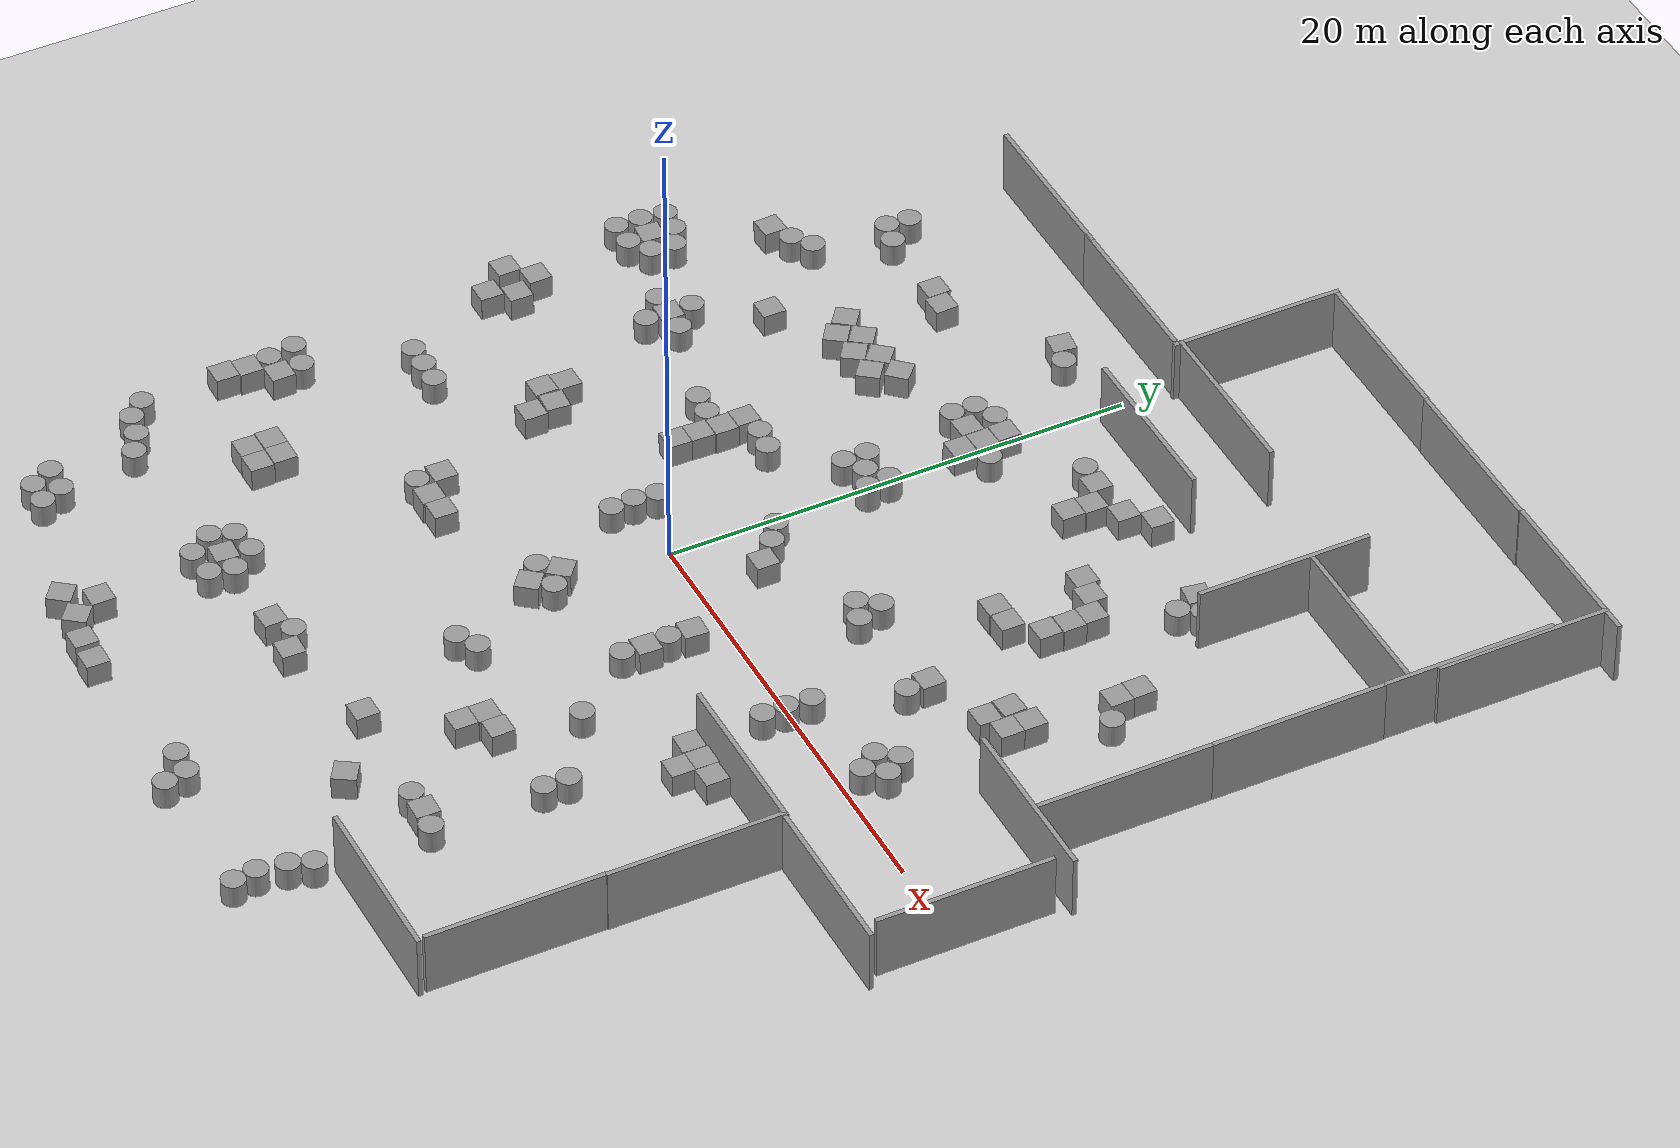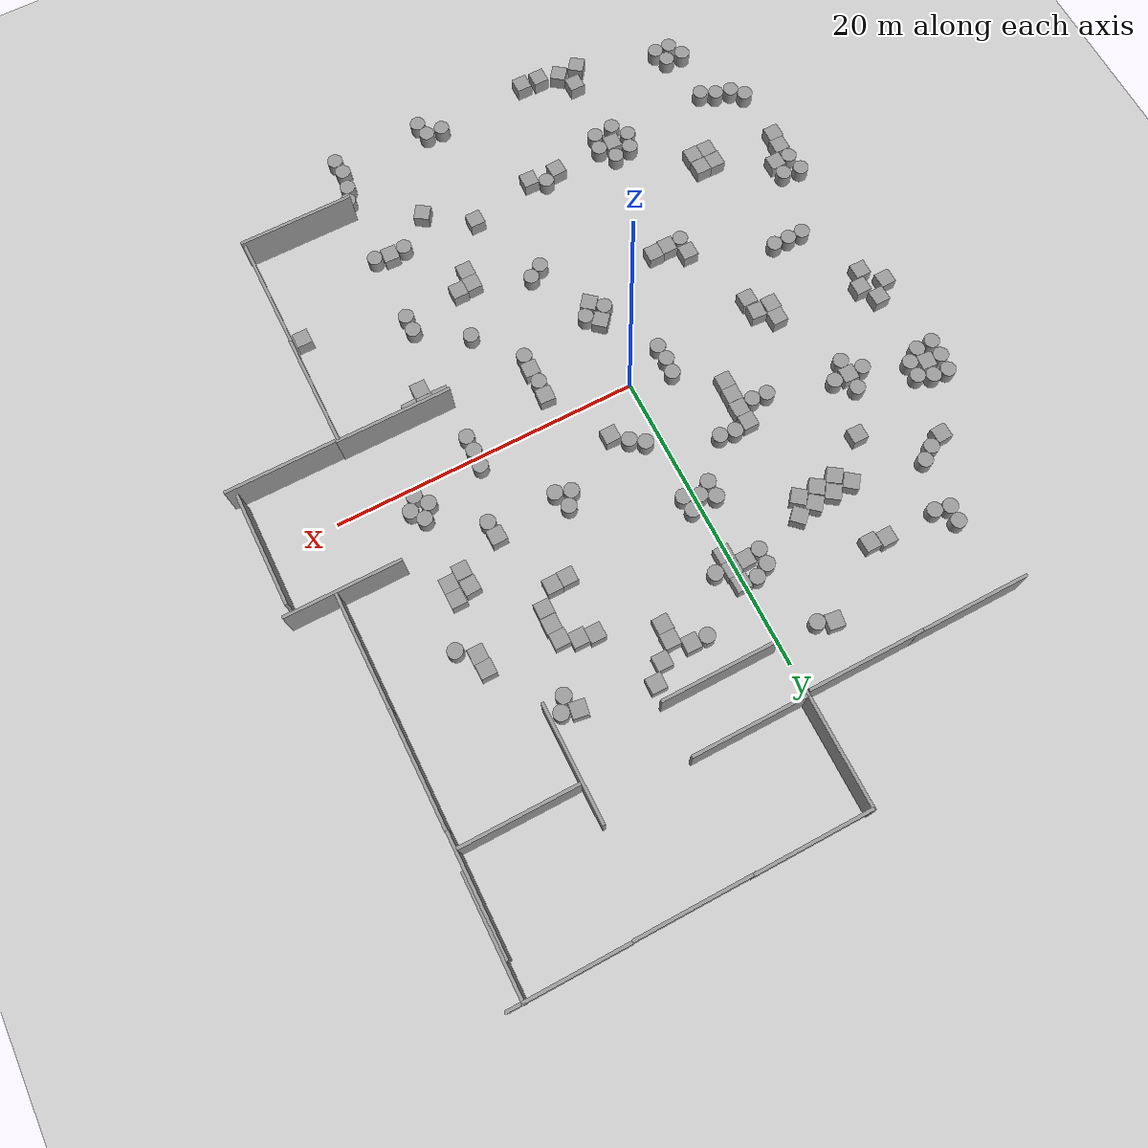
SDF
<sdf version="1.6">
 <world name="default">
  <light name="sun" type="directional">
   <pose>0 0 10 0 -0 0</pose>
   <diffuse>0.8 0.8 0.8 1</diffuse>
   <specular>0.1 0.1 0.1 1</specular>
   <attenuation>
    <range>1000</range>
    <constant>0.9</constant>
    <linear>0.01</linear>
    <quadratic>0.001</quadratic>
   </attenuation>
   <direction>-0.5 0.5 -1</direction>
  </light>
  <model name="ground_plane">
   <static>1</static>
   <link name="link">
    <collision name="collision">
     <geometry><plane><normal>0 0 1</normal><size>100 100</size></plane></geometry>
     <surface><friction><ode><mu>100</mu><mu2>50</mu2></ode></friction></surface>
    </collision>
    <visual name="visual">
     <cast_shadows>0</cast_shadows>
     <geometry><plane><normal>0 0 1</normal><size>100 100</size></plane></geometry>
     <material>
      <script><uri>file://media/materials/scripts/gazebo.material</uri><name>Gazebo/Grey</name></script>
     </material>
    </visual>
   </link>
  </model>
  <gravity>0 0 -9.8</gravity>
  <magnetic_field>6e-06 2.3e-05 -4.2e-05</magnetic_field>
  <atmosphere type="adiabatic"/>
  <physics name="default_physics" default="0" type="ode">
   <max_step_size>0.003</max_step_size>
   <real_time_factor>2</real_time_factor>
   <real_time_update_rate>1000</real_time_update_rate>
  </physics>
  <scene><ambient>0.4 0.4 0.4 1</ambient><background>0.7 0.7 0.7 1</background><shadows>1</shadows></scene>
  <spherical_coordinates>
   <surface_model>EARTH_WGS84</surface_model>
   <latitude_deg>0</latitude_deg>
   <longitude_deg>0</longitude_deg>
   <elevation>0</elevation>
   <heading_deg>0</heading_deg>
  </spherical_coordinates>
  <model name="unit_box_1">
   <pose>-5.0981 4.77867 0.5 0 0 -0.005236</pose>
   <link name="link">
    <inertial>
     <mass>1</mass>
     <inertia>
      <ixx>0.166667</ixx>
      <ixy>0</ixy>
      <ixz>0</ixz>
      <iyy>0.166667</iyy>
      <iyz>0</iyz>
      <izz>0.166667</izz>
     </inertia>
    </inertial>
    <collision name="collision"><geometry><box><size>1 1 1</size></box></geometry></collision>
    <visual name="visual">
     <geometry><box><size>1 1 1</size></box></geometry>
     <material>
      <script><name>Gazebo/Grey</name><uri>file://media/materials/scripts/gazebo.material</uri></script>
     </material>
    </visual>
   </link>
  </model>
  <model name="unit_box_2">
   <pose>-5.14808 3.76937 0.5 0 0 -0.018732</pose>
   <link name="link">
    <inertial>
     <mass>1</mass>
     <inertia>
      <ixx>0.166667</ixx>
      <ixy>0</ixy>
      <ixz>0</ixz>
      <iyy>0.166667</iyy>
      <iyz>0</iyz>
      <izz>0.166667</izz>
     </inertia>
    </inertial>
    <collision name="collision"><geometry><box><size>1 1 1</size></box></geometry></collision>
    <visual name="visual">
     <geometry><box><size>1 1 1</size></box></geometry>
     <material>
      <script><name>Gazebo/Grey</name><uri>file://media/materials/scripts/gazebo.material</uri></script>
     </material>
    </visual>
   </link>
  </model>
  <model name="unit_box_5">
   <pose>-6.51998 -7.31504 0.5 0 0 -0.011529</pose>
   <link name="link">
    <inertial>
     <mass>1</mass>
     <inertia>
      <ixx>0.166667</ixx>
      <ixy>0</ixy>
      <ixz>0</ixz>
      <iyy>0.166667</iyy>
      <iyz>0</iyz>
      <izz>0.166667</izz>
     </inertia>
    </inertial>
    <collision name="collision"><geometry><box><size>1 1 1</size></box></geometry></collision>
    <visual name="visual">
     <geometry><box><size>1 1 1</size></box></geometry>
     <material>
      <script><name>Gazebo/Grey</name><uri>file://media/materials/scripts/gazebo.material</uri></script>
     </material>
    </visual>
   </link>
  </model>
  <model name="unit_cylinder_0">
   <pose>10.6658 -0.256071 0.499942 0 0 -3.1e-05</pose>
   <link name="link">
    <inertial>
     <mass>1</mass>
     <inertia><ixx>0.145833</ixx><ixy>0</ixy><ixz>0</ixz><iyy>0.145833</iyy><iyz>0</iyz><izz>0.125</izz></inertia>
    </inertial>
    <collision name="collision">
     <geometry><cylinder><radius>0.5</radius><length>1</length></cylinder></geometry>
    </collision>
    <visual name="visual">
     <geometry><cylinder><radius>0.5</radius><length>1</length></cylinder></geometry>
     <material>
      <script><name>Gazebo/Grey</name><uri>file://media/materials/scripts/gazebo.material</uri></script>
     </material>
    </visual>
   </link>
  </model>
  <model name="unit_cylinder_1">
   <pose>10.5673 -10.4506 0.499942 0 0 -0.000248</pose>
   <link name="link">
    <inertial>
     <mass>1</mass>
     <inertia><ixx>0.145833</ixx><ixy>0</ixy><ixz>0</ixz><iyy>0.145833</iyy><iyz>0</iyz><izz>0.125</izz></inertia>
    </inertial>
    <collision name="collision">
     <geometry><cylinder><radius>0.5</radius><length>1</length></cylinder></geometry>
    </collision>
    <visual name="visual">
     <geometry><cylinder><radius>0.5</radius><length>1</length></cylinder></geometry>
     <material>
      <script><name>Gazebo/Grey</name><uri>file://media/materials/scripts/gazebo.material</uri></script>
     </material>
    </visual>
   </link>
  </model>
  <model name="unit_cylinder_2">
   <pose>10.5614 -9.39908 0.499942 0 0 -0.000915</pose>
   <link name="link">
    <inertial>
     <mass>1</mass>
     <inertia><ixx>0.145833</ixx><ixy>0</ixy><ixz>0</ixz><iyy>0.145833</iyy><iyz>0</iyz><izz>0.125</izz></inertia>
    </inertial>
    <collision name="collision">
     <geometry><cylinder><radius>0.5</radius><length>1</length></cylinder></geometry>
    </collision>
    <visual name="visual">
     <geometry><cylinder><radius>0.5</radius><length>1</length></cylinder></geometry>
     <material>
      <script><name>Gazebo/Grey</name><uri>file://media/materials/scripts/gazebo.material</uri></script>
     </material>
    </visual>
   </link>
  </model>
  <model name="unit_cylinder_3">
   <pose>10.6756 -1.25603 0.499942 0 0 -5.6e-05</pose>
   <link name="link">
    <inertial>
     <mass>1</mass>
     <inertia><ixx>0.145833</ixx><ixy>0</ixy><ixz>0</ixz><iyy>0.145833</iyy><iyz>0</iyz><izz>0.125</izz></inertia>
    </inertial>
    <collision name="collision">
     <geometry><cylinder><radius>0.5</radius><length>1</length></cylinder></geometry>
    </collision>
    <visual name="visual">
     <geometry><cylinder><radius>0.5</radius><length>1</length></cylinder></geometry>
     <material>
      <script><name>Gazebo/Grey</name><uri>file://media/materials/scripts/gazebo.material</uri></script>
     </material>
    </visual>
   </link>
  </model>
  <model name="unit_cylinder_4">
   <pose>10.7381 0.821389 0.499942 0 -0 0</pose>
   <link name="link">
    <inertial>
     <mass>1</mass>
     <inertia><ixx>0.145833</ixx><ixy>0</ixy><ixz>0</ixz><iyy>0.145833</iyy><iyz>0</iyz><izz>0.125</izz></inertia>
    </inertial>
    <collision name="collision">
     <geometry><cylinder><radius>0.5</radius><length>1</length></cylinder></geometry>
    </collision>
    <visual name="visual">
     <geometry><cylinder><radius>0.5</radius><length>1</length></cylinder></geometry>
     <material>
      <script><name>Gazebo/Grey</name><uri>file://media/materials/scripts/gazebo.material</uri></script>
     </material>
    </visual>
   </link>
  </model>
  <model name="unit_box_8">
   <pose>-9.3394 -0.542282 0.5 0 0 -0.074034</pose>
   <link name="link">
    <inertial>
     <mass>1</mass>
     <inertia>
      <ixx>0.166667</ixx>
      <ixy>0</ixy>
      <ixz>0</ixz>
      <iyy>0.166667</iyy>
      <iyz>0</iyz>
      <izz>0.166667</izz>
     </inertia>
    </inertial>
    <collision name="collision"><geometry><box><size>1 1 1</size></box></geometry></collision>
    <visual name="visual">
     <geometry><box><size>1 1 1</size></box></geometry>
     <material>
      <script><name>Gazebo/Grey</name><uri>file://media/materials/scripts/gazebo.material</uri></script>
     </material>
    </visual>
   </link>
  </model>
  <model name="unit_cylinder_6">
   <pose>-2.57686 0.723564 0.499942 0 0 -0.000453</pose>
   <link name="link">
    <inertial>
     <mass>1</mass>
     <inertia><ixx>0.145833</ixx><ixy>0</ixy><ixz>0</ixz><iyy>0.145833</iyy><iyz>0</iyz><izz>0.125</izz></inertia>
    </inertial>
    <collision name="collision">
     <geometry><cylinder><radius>0.5</radius><length>1</length></cylinder></geometry>
    </collision>
    <visual name="visual">
     <geometry><cylinder><radius>0.5</radius><length>1</length></cylinder></geometry>
     <material>
      <script><name>Gazebo/Grey</name><uri>file://media/materials/scripts/gazebo.material</uri></script>
     </material>
    </visual>
   </link>
  </model>
  <model name="unit_box_9">
   <pose>2.80573 2.69051 0.5 0 0 -0.00823</pose>
   <link name="link">
    <inertial>
     <mass>1</mass>
     <inertia>
      <ixx>0.166667</ixx>
      <ixy>0</ixy>
      <ixz>0</ixz>
      <iyy>0.166667</iyy>
      <iyz>0</iyz>
      <izz>0.166667</izz>
     </inertia>
    </inertial>
    <collision name="collision"><geometry><box><size>1 1 1</size></box></geometry></collision>
    <visual name="visual">
     <geometry><box><size>1 1 1</size></box></geometry>
     <material>
      <script><name>Gazebo/Grey</name><uri>file://media/materials/scripts/gazebo.material</uri></script>
     </material>
    </visual>
   </link>
  </model>
  <model name="unit_cylinder_7">
   <pose>1.40059 -9.83483 0.499942 0 -0 3.6e-05</pose>
   <link name="link">
    <inertial>
     <mass>1</mass>
     <inertia><ixx>0.145833</ixx><ixy>0</ixy><ixz>0</ixz><iyy>0.145833</iyy><iyz>0</iyz><izz>0.125</izz></inertia>
    </inertial>
    <collision name="collision">
     <geometry><cylinder><radius>0.5</radius><length>1</length></cylinder></geometry>
    </collision>
    <visual name="visual">
     <geometry><cylinder><radius>0.5</radius><length>1</length></cylinder></geometry>
     <material>
      <script><name>Gazebo/Grey</name><uri>file://media/materials/scripts/gazebo.material</uri></script>
     </material>
    </visual>
   </link>
  </model>
  <model name="unit_box_10">
   <pose>6.83779 -10.6025 0.5 0 -0 1.5e-05</pose>
   <link name="link">
    <inertial>
     <mass>1</mass>
     <inertia>
      <ixx>0.166667</ixx>
      <ixy>0</ixy>
      <ixz>0</ixz>
      <iyy>0.166667</iyy>
      <iyz>0</iyz>
      <izz>0.166667</izz>
     </inertia>
    </inertial>
    <collision name="collision"><geometry><box><size>1 1 1</size></box></geometry></collision>
    <visual name="visual">
     <geometry><box><size>1 1 1</size></box></geometry>
     <material>
      <script><name>Gazebo/Grey</name><uri>file://media/materials/scripts/gazebo.material</uri></script>
     </material>
    </visual>
   </link>
  </model>
  <model name="unit_box_11">
   <pose>5.82223 -11.6823 0.499964 7.2e-05 0 -2.5e-05</pose>
   <link name="link">
    <inertial>
     <mass>1</mass>
     <inertia>
      <ixx>0.166667</ixx>
      <ixy>0</ixy>
      <ixz>0</ixz>
      <iyy>0.166667</iyy>
      <iyz>0</iyz>
      <izz>0.166667</izz>
     </inertia>
    </inertial>
    <collision name="collision"><geometry><box><size>1 1 1</size></box></geometry></collision>
    <visual name="visual">
     <geometry><box><size>1 1 1</size></box></geometry>
     <material>
      <script><name>Gazebo/Grey</name><uri>file://media/materials/scripts/gazebo.material</uri></script>
     </material>
    </visual>
   </link>
  </model>
  <model name="unit_cylinder_8_0">
   <pose>-0.197454 8.65118 0.499942 0 0 -0.115703</pose>
   <link name="link">
    <inertial>
     <mass>1</mass>
     <inertia><ixx>0.145833</ixx><ixy>0</ixy><ixz>0</ixz><iyy>0.145833</iyy><iyz>0</iyz><izz>0.125</izz></inertia>
    </inertial>
    <collision name="collision">
     <geometry><cylinder><radius>0.5</radius><length>1</length></cylinder></geometry>
    </collision>
    <visual name="visual">
     <geometry><cylinder><radius>0.5</radius><length>1</length></cylinder></geometry>
     <material>
      <script><name>Gazebo/Grey</name><uri>file://media/materials/scripts/gazebo.material</uri></script>
     </material>
    </visual>
   </link>
  </model>
  <model name="unit_box_12">
   <pose>5.15719 -1.54455 0.5 0 0 -0.056719</pose>
   <link name="link">
    <inertial>
     <mass>1</mass>
     <inertia>
      <ixx>0.166667</ixx>
      <ixy>0</ixy>
      <ixz>0</ixz>
      <iyy>0.166667</iyy>
      <iyz>0</iyz>
      <izz>0.166667</izz>
     </inertia>
    </inertial>
    <collision name="collision"><geometry><box><size>1 1 1</size></box></geometry></collision>
    <visual name="visual">
     <geometry><box><size>1 1 1</size></box></geometry>
     <material>
      <script><name>Gazebo/Grey</name><uri>file://media/materials/scripts/gazebo.material</uri></script>
     </material>
    </visual>
   </link>
  </model>
  <model name="unit_cylinder_8_1">
   <pose>5.09818 -2.54286 0.499942 0 0 -0.000551</pose>
   <link name="link">
    <inertial>
     <mass>1</mass>
     <inertia><ixx>0.145833</ixx><ixy>0</ixy><ixz>0</ixz><iyy>0.145833</iyy><iyz>0</iyz><izz>0.125</izz></inertia>
    </inertial>
    <collision name="collision">
     <geometry><cylinder><radius>0.5</radius><length>1</length></cylinder></geometry>
    </collision>
    <visual name="visual">
     <geometry><cylinder><radius>0.5</radius><length>1</length></cylinder></geometry>
     <material>
      <script><name>Gazebo/Grey</name><uri>file://media/materials/scripts/gazebo.material</uri></script>
     </material>
    </visual>
   </link>
  </model>
  <model name="unit_box_13">
   <pose>5.186 -3.54449 0.5 0 0 -0.016738</pose>
   <link name="link">
    <inertial>
     <mass>1</mass>
     <inertia>
      <ixx>0.166667</ixx>
      <ixy>0</ixy>
      <ixz>0</ixz>
      <iyy>0.166667</iyy>
      <iyz>0</iyz>
      <izz>0.166667</izz>
     </inertia>
    </inertial>
    <collision name="collision"><geometry><box><size>1 1 1</size></box></geometry></collision>
    <visual name="visual">
     <geometry><box><size>1 1 1</size></box></geometry>
     <material>
      <script><name>Gazebo/Grey</name><uri>file://media/materials/scripts/gazebo.material</uri></script>
     </material>
    </visual>
   </link>
  </model>
  <model name="unit_cylinder_8_2">
   <pose>5.13166 -4.54376 0.499942 0 0 -0.000328</pose>
   <link name="link">
    <inertial>
     <mass>1</mass>
     <inertia><ixx>0.145833</ixx><ixy>0</ixy><ixz>0</ixz><iyy>0.145833</iyy><iyz>0</iyz><izz>0.125</izz></inertia>
    </inertial>
    <collision name="collision">
     <geometry><cylinder><radius>0.5</radius><length>1</length></cylinder></geometry>
    </collision>
    <visual name="visual">
     <geometry><cylinder><radius>0.5</radius><length>1</length></cylinder></geometry>
     <material>
      <script><name>Gazebo/Grey</name><uri>file://media/materials/scripts/gazebo.material</uri></script>
     </material>
    </visual>
   </link>
  </model>
  <model name="unit_box_14">
   <pose>5.83775 -10.6823 0.499964 -7.3e-05 0 -2.8e-05</pose>
   <link name="link">
    <inertial>
     <mass>1</mass>
     <inertia>
      <ixx>0.166667</ixx>
      <ixy>0</ixy>
      <ixz>0</ixz>
      <iyy>0.166667</iyy>
      <iyz>0</iyz>
      <izz>0.166667</izz>
     </inertia>
    </inertial>
    <collision name="collision"><geometry><box><size>1 1 1</size></box></geometry></collision>
    <visual name="visual">
     <geometry><box><size>1 1 1</size></box></geometry>
     <material>
      <script><name>Gazebo/Grey</name><uri>file://media/materials/scripts/gazebo.material</uri></script>
     </material>
    </visual>
   </link>
  </model>
  <model name="unit_box_15">
   <pose>-10.3952 -0.600275 0.5 0 0 -0.001077</pose>
   <link name="link">
    <inertial>
     <mass>1</mass>
     <inertia>
      <ixx>0.166667</ixx>
      <ixy>0</ixy>
      <ixz>0</ixz>
      <iyy>0.166667</iyy>
      <iyz>0</iyz>
      <izz>0.166667</izz>
     </inertia>
    </inertial>
    <collision name="collision"><geometry><box><size>1 1 1</size></box></geometry></collision>
    <visual name="visual">
     <geometry><box><size>1 1 1</size></box></geometry>
     <material>
      <script><name>Gazebo/Grey</name><uri>file://media/materials/scripts/gazebo.material</uri></script>
     </material>
    </visual>
   </link>
  </model>
  <model name="unit_box_23">
   <pose>9.27784 13.3025 0.5 0 0 -0.004142</pose>
   <link name="link">
    <inertial>
     <mass>1</mass>
     <inertia>
      <ixx>0.166667</ixx>
      <ixy>0</ixy>
      <ixz>0</ixz>
      <iyy>0.166667</iyy>
      <iyz>0</iyz>
      <izz>0.166667</izz>
     </inertia>
    </inertial>
    <collision name="collision"><geometry><box><size>1 1 1</size></box></geometry></collision>
    <visual name="visual">
     <geometry><box><size>1 1 1</size></box></geometry>
     <material>
      <script><name>Gazebo/Grey</name><uri>file://media/materials/scripts/gazebo.material</uri></script>
     </material>
    </visual>
   </link>
  </model>
  <model name="unit_cylinder_13">
   <pose>14.5459 1.57194 0.499942 0 -0 0.013715</pose>
   <link name="link">
    <inertial>
     <mass>1</mass>
     <inertia><ixx>0.145833</ixx><ixy>0</ixy><ixz>0</ixz><iyy>0.145833</iyy><iyz>0</iyz><izz>0.125</izz></inertia>
    </inertial>
    <collision name="collision">
     <geometry><cylinder><radius>0.5</radius><length>1</length></cylinder></geometry>
    </collision>
    <visual name="visual">
     <geometry><cylinder><radius>0.5</radius><length>1</length></cylinder></geometry>
     <material>
      <script><name>Gazebo/Grey</name><uri>file://media/materials/scripts/gazebo.material</uri></script>
     </material>
    </visual>
   </link>
  </model>
  <model name="unit_box_26">
   <pose>3.65039 -14.8069 0.5 0 -0 0</pose>
   <link name="link">
    <inertial>
     <mass>1</mass>
     <inertia>
      <ixx>0.166667</ixx>
      <ixy>0</ixy>
      <ixz>0</ixz>
      <iyy>0.166667</iyy>
      <iyz>0</iyz>
      <izz>0.166667</izz>
     </inertia>
    </inertial>
    <collision name="collision"><geometry><box><size>1 1 1</size></box></geometry></collision>
    <visual name="visual">
     <geometry><box><size>1 1 1</size></box></geometry>
     <material>
      <script><name>Gazebo/Grey</name><uri>file://media/materials/scripts/gazebo.material</uri></script>
     </material>
    </visual>
   </link>
  </model>
  <model name="unit_cylinder_15">
   <pose>-1.77956 -15.2792 0.499942 0 0 -0.00561</pose>
   <link name="link">
    <inertial>
     <mass>1</mass>
     <inertia><ixx>0.145833</ixx><ixy>0</ixy><ixz>0</ixz><iyy>0.145833</iyy><iyz>0</iyz><izz>0.125</izz></inertia>
    </inertial>
    <collision name="collision">
     <geometry><cylinder><radius>0.5</radius><length>1</length></cylinder></geometry>
    </collision>
    <visual name="visual">
     <geometry><cylinder><radius>0.5</radius><length>1</length></cylinder></geometry>
     <material>
      <script><name>Gazebo/Grey</name><uri>file://media/materials/scripts/gazebo.material</uri></script>
     </material>
    </visual>
   </link>
  </model>
  <model name="unit_box_27">
   <pose>-7.00414 -15.9171 0.5 0 0 -0.05005</pose>
   <link name="link">
    <inertial>
     <mass>1</mass>
     <inertia>
      <ixx>0.166667</ixx>
      <ixy>0</ixy>
      <ixz>0</ixz>
      <iyy>0.166667</iyy>
      <iyz>0</iyz>
      <izz>0.166667</izz>
     </inertia>
    </inertial>
    <collision name="collision"><geometry><box><size>1 1 1</size></box></geometry></collision>
    <visual name="visual">
     <geometry><box><size>1 1 1</size></box></geometry>
     <material>
      <script><name>Gazebo/Grey</name><uri>file://media/materials/scripts/gazebo.material</uri></script>
     </material>
    </visual>
   </link>
  </model>
  <model name="unit_cylinder_19">
   <pose>15.725 1.55357 0.499942 0 -0 0.002059</pose>
   <link name="link">
    <inertial>
     <mass>1</mass>
     <inertia><ixx>0.145833</ixx><ixy>0</ixy><ixz>0</ixz><iyy>0.145833</iyy><iyz>0</iyz><izz>0.125</izz></inertia>
    </inertial>
    <collision name="collision">
     <geometry><cylinder><radius>0.5</radius><length>1</length></cylinder></geometry>
    </collision>
    <visual name="visual">
     <geometry><cylinder><radius>0.5</radius><length>1</length></cylinder></geometry>
     <material>
      <script><name>Gazebo/Grey</name><uri>file://media/materials/scripts/gazebo.material</uri></script>
     </material>
    </visual>
   </link>
  </model>
  <model name="unit_box_30">
   <pose>15.8822 11.2878 0.5 0 -0 0.004435</pose>
   <link name="link">
    <inertial>
     <mass>1</mass>
     <inertia>
      <ixx>0.166667</ixx>
      <ixy>0</ixy>
      <ixz>0</ixz>
      <iyy>0.166667</iyy>
      <iyz>0</iyz>
      <izz>0.166667</izz>
     </inertia>
    </inertial>
    <collision name="collision"><geometry><box><size>1 1 1</size></box></geometry></collision>
    <visual name="visual">
     <geometry><box><size>1 1 1</size></box></geometry>
     <material>
      <script><name>Gazebo/Grey</name><uri>file://media/materials/scripts/gazebo.material</uri></script>
     </material>
    </visual>
   </link>
  </model>
  <model name="unit_cylinder_20">
   <pose>16.9697 10.5115 0.499942 0 -0 0</pose>
   <link name="link">
    <inertial>
     <mass>1</mass>
     <inertia><ixx>0.145833</ixx><ixy>0</ixy><ixz>0</ixz><iyy>0.145833</iyy><iyz>0</iyz><izz>0.125</izz></inertia>
    </inertial>
    <collision name="collision">
     <geometry><cylinder><radius>0.5</radius><length>1</length></cylinder></geometry>
    </collision>
    <visual name="visual">
     <geometry><cylinder><radius>0.5</radius><length>1</length></cylinder></geometry>
     <material>
      <script><name>Gazebo/Grey</name><uri>file://media/materials/scripts/gazebo.material</uri></script>
     </material>
    </visual>
   </link>
  </model>
  <model name="unit_box_32">
   <pose>10.2771 13.1126 0.5 0 0 -0.00417</pose>
   <link name="link">
    <inertial>
     <mass>1</mass>
     <inertia>
      <ixx>0.166667</ixx>
      <ixy>0</ixy>
      <ixz>0</ixz>
      <iyy>0.166667</iyy>
      <iyz>0</iyz>
      <izz>0.166667</izz>
     </inertia>
    </inertial>
    <collision name="collision"><geometry><box><size>1 1 1</size></box></geometry></collision>
    <visual name="visual">
     <geometry><box><size>1 1 1</size></box></geometry>
     <material>
      <script><name>Gazebo/Grey</name><uri>file://media/materials/scripts/gazebo.material</uri></script>
     </material>
    </visual>
   </link>
  </model>
  <model name="unit_cylinder_26">
   <pose>-2.6867 -0.270452 0.499942 0 -0 0.002292</pose>
   <link name="link">
    <inertial>
     <mass>1</mass>
     <inertia><ixx>0.145833</ixx><ixy>0</ixy><ixz>0</ixz><iyy>0.145833</iyy><iyz>0</iyz><izz>0.125</izz></inertia>
    </inertial>
    <collision name="collision">
     <geometry><cylinder><radius>0.5</radius><length>1</length></cylinder></geometry>
    </collision>
    <visual name="visual">
     <geometry><cylinder><radius>0.5</radius><length>1</length></cylinder></geometry>
     <material>
      <script><name>Gazebo/Grey</name><uri>file://media/materials/scripts/gazebo.material</uri></script>
     </material>
    </visual>
   </link>
  </model>
  <model name="unit_box_24_0">
   <pose>14.5253 7.36912 0.5 0 -0 0.049836</pose>
   <link name="link">
    <inertial>
     <mass>1</mass>
     <inertia>
      <ixx>0.166667</ixx>
      <ixy>0</ixy>
      <ixz>0</ixz>
      <iyy>0.166667</iyy>
      <iyz>0</iyz>
      <izz>0.166667</izz>
     </inertia>
    </inertial>
    <collision name="collision"><geometry><box><size>1 1 1</size></box></geometry></collision>
    <visual name="visual">
     <geometry><box><size>1 1 1</size></box></geometry>
     <material>
      <script><name>Gazebo/Grey</name><uri>file://media/materials/scripts/gazebo.material</uri></script>
     </material>
    </visual>
   </link>
  </model>
  <model name="unit_box_24_1">
   <pose>14.5739 6.30414 0.5 0 -0 0.003533</pose>
   <link name="link">
    <inertial>
     <mass>1</mass>
     <inertia>
      <ixx>0.166667</ixx>
      <ixy>0</ixy>
      <ixz>0</ixz>
      <iyy>0.166667</iyy>
      <iyz>0</iyz>
      <izz>0.166667</izz>
     </inertia>
    </inertial>
    <collision name="collision"><geometry><box><size>1 1 1</size></box></geometry></collision>
    <visual name="visual">
     <geometry><box><size>1 1 1</size></box></geometry>
     <material>
      <script><name>Gazebo/Grey</name><uri>file://media/materials/scripts/gazebo.material</uri></script>
     </material>
    </visual>
   </link>
  </model>
  <model name="unit_box_28_0">
   <pose>-16.7585 -10.5798 0.5 0 0 -0.00305</pose>
   <link name="link">
    <inertial>
     <mass>1</mass>
     <inertia>
      <ixx>0.166667</ixx>
      <ixy>0</ixy>
      <ixz>0</ixz>
      <iyy>0.166667</iyy>
      <iyz>0</iyz>
      <izz>0.166667</izz>
     </inertia>
    </inertial>
    <collision name="collision"><geometry><box><size>1 1 1</size></box></geometry></collision>
    <visual name="visual">
     <geometry><box><size>1 1 1</size></box></geometry>
     <material>
      <script><name>Gazebo/Grey</name><uri>file://media/materials/scripts/gazebo.material</uri></script>
     </material>
    </visual>
   </link>
  </model>
  <model name="unit_box_28_1">
   <pose>-16.8635 -11.5795 0.5 0 0 -0.003058</pose>
   <link name="link">
    <inertial>
     <mass>1</mass>
     <inertia>
      <ixx>0.166667</ixx>
      <ixy>0</ixy>
      <ixz>0</ixz>
      <iyy>0.166667</iyy>
      <iyz>0</iyz>
      <izz>0.166667</izz>
     </inertia>
    </inertial>
    <collision name="collision"><geometry><box><size>1 1 1</size></box></geometry></collision>
    <visual name="visual">
     <geometry><box><size>1 1 1</size></box></geometry>
     <material>
      <script><name>Gazebo/Grey</name><uri>file://media/materials/scripts/gazebo.material</uri></script>
     </material>
    </visual>
   </link>
  </model>
  <model name="unit_cylinder_27">
   <pose>-16.0304 -15.9217 0.499942 0 0 -4.4e-05</pose>
   <link name="link">
    <inertial>
     <mass>1</mass>
     <inertia><ixx>0.145833</ixx><ixy>0</ixy><ixz>0</ixz><iyy>0.145833</iyy><iyz>0</iyz><izz>0.125</izz></inertia>
    </inertial>
    <collision name="collision">
     <geometry><cylinder><radius>0.5</radius><length>1</length></cylinder></geometry>
    </collision>
    <visual name="visual">
     <geometry><cylinder><radius>0.5</radius><length>1</length></cylinder></geometry>
     <material>
      <script><name>Gazebo/Grey</name><uri>file://media/materials/scripts/gazebo.material</uri></script>
     </material>
    </visual>
   </link>
  </model>
  <model name="unit_cylinder_28">
   <pose>-15.0122 -16.1585 0.499942 0 -0 0</pose>
   <link name="link">
    <inertial>
     <mass>1</mass>
     <inertia><ixx>0.145833</ixx><ixy>0</ixy><ixz>0</ixz><iyy>0.145833</iyy><iyz>0</iyz><izz>0.125</izz></inertia>
    </inertial>
    <collision name="collision">
     <geometry><cylinder><radius>0.5</radius><length>1</length></cylinder></geometry>
    </collision>
    <visual name="visual">
     <geometry><cylinder><radius>0.5</radius><length>1</length></cylinder></geometry>
     <material>
      <script><name>Gazebo/Grey</name><uri>file://media/materials/scripts/gazebo.material</uri></script>
     </material>
    </visual>
   </link>
  </model>
  <model name="unit_cylinder_29">
   <pose>-14.0775 -16.6533 0.499942 0 -0 0</pose>
   <link name="link">
    <inertial>
     <mass>1</mass>
     <inertia><ixx>0.145833</ixx><ixy>0</ixy><ixz>0</ixz><iyy>0.145833</iyy><iyz>0</iyz><izz>0.125</izz></inertia>
    </inertial>
    <collision name="collision">
     <geometry><cylinder><radius>0.5</radius><length>1</length></cylinder></geometry>
    </collision>
    <visual name="visual">
     <geometry><cylinder><radius>0.5</radius><length>1</length></cylinder></geometry>
     <material>
      <script><name>Gazebo/Grey</name><uri>file://media/materials/scripts/gazebo.material</uri></script>
     </material>
    </visual>
   </link>
  </model>
  <model name="unit_box_28">
   <pose>-15.8992 -9.57782 0.5 0 -0 0.005949</pose>
   <link name="link">
    <inertial>
     <mass>1</mass>
     <inertia>
      <ixx>0.166667</ixx>
      <ixy>0</ixy>
      <ixz>0</ixz>
      <iyy>0.166667</iyy>
      <iyz>0</iyz>
      <izz>0.166667</izz>
     </inertia>
    </inertial>
    <collision name="collision"><geometry><box><size>1 1 1</size></box></geometry></collision>
    <visual name="visual">
     <geometry><box><size>1 1 1</size></box></geometry>
     <material>
      <script><name>Gazebo/Grey</name><uri>file://media/materials/scripts/gazebo.material</uri></script>
     </material>
    </visual>
   </link>
  </model>
  <model name="unit_box_34">
   <pose>-9.24528 -1.60585 0.5 0 -0 0</pose>
   <link name="link">
    <inertial>
     <mass>1</mass>
     <inertia>
      <ixx>0.166667</ixx>
      <ixy>0</ixy>
      <ixz>0</ixz>
      <iyy>0.166667</iyy>
      <iyz>0</iyz>
      <izz>0.166667</izz>
     </inertia>
    </inertial>
    <collision name="collision"><geometry><box><size>1 1 1</size></box></geometry></collision>
    <visual name="visual">
     <geometry><box><size>1 1 1</size></box></geometry>
     <material>
      <script><name>Gazebo/Grey</name><uri>file://media/materials/scripts/gazebo.material</uri></script>
     </material>
    </visual>
   </link>
  </model>
  <model name="unit_box_37">
   <pose>-12.2689 5.91862 0.5 0 0 -0.024908</pose>
   <link name="link">
    <inertial>
     <mass>1</mass>
     <inertia>
      <ixx>0.166667</ixx>
      <ixy>0</ixy>
      <ixz>0</ixz>
      <iyy>0.166667</iyy>
      <iyz>0</iyz>
      <izz>0.166667</izz>
     </inertia>
    </inertial>
    <collision name="collision"><geometry><box><size>1 1 1</size></box></geometry></collision>
    <visual name="visual">
     <geometry><box><size>1 1 1</size></box></geometry>
     <material>
      <script><name>Gazebo/Grey</name><uri>file://media/materials/scripts/gazebo.material</uri></script>
     </material>
    </visual>
   </link>
  </model>
  <model name="unit_cylinder_32">
   <pose>-13.2104 16.2333 0.499942 0 -0 0.006978</pose>
   <link name="link">
    <inertial>
     <mass>1</mass>
     <inertia><ixx>0.145833</ixx><ixy>0</ixy><ixz>0</ixz><iyy>0.145833</iyy><iyz>0</iyz><izz>0.125</izz></inertia>
    </inertial>
    <collision name="collision">
     <geometry><cylinder><radius>0.5</radius><length>1</length></cylinder></geometry>
    </collision>
    <visual name="visual">
     <geometry><cylinder><radius>0.5</radius><length>1</length></cylinder></geometry>
     <material>
      <script><name>Gazebo/Grey</name><uri>file://media/materials/scripts/gazebo.material</uri></script>
     </material>
    </visual>
   </link>
  </model>
  <model name="unit_cylinder_33">
   <pose>-13.1457 17.2313 0.499942 0 0 -0.001377</pose>
   <link name="link">
    <inertial>
     <mass>1</mass>
     <inertia><ixx>0.145833</ixx><ixy>0</ixy><ixz>0</ixz><iyy>0.145833</iyy><iyz>0</iyz><izz>0.125</izz></inertia>
    </inertial>
    <collision name="collision">
     <geometry><cylinder><radius>0.5</radius><length>1</length></cylinder></geometry>
    </collision>
    <visual name="visual">
     <geometry><cylinder><radius>0.5</radius><length>1</length></cylinder></geometry>
     <material>
      <script><name>Gazebo/Grey</name><uri>file://media/materials/scripts/gazebo.material</uri></script>
     </material>
    </visual>
   </link>
  </model>
  <model name="unit_cylinder_34">
   <pose>-2.61658 -1.268 0.499942 0 0 -0.0024</pose>
   <link name="link">
    <inertial>
     <mass>1</mass>
     <inertia><ixx>0.145833</ixx><ixy>0</ixy><ixz>0</ixz><iyy>0.145833</iyy><iyz>0</iyz><izz>0.125</izz></inertia>
    </inertial>
    <collision name="collision">
     <geometry><cylinder><radius>0.5</radius><length>1</length></cylinder></geometry>
    </collision>
    <visual name="visual">
     <geometry><cylinder><radius>0.5</radius><length>1</length></cylinder></geometry>
     <material>
      <script><name>Gazebo/Grey</name><uri>file://media/materials/scripts/gazebo.material</uri></script>
     </material>
    </visual>
   </link>
  </model>
  <model name="unit_cylinder_40">
   <pose>8.62202 -15.0706 0.499942 0 0 -0.007938</pose>
   <link name="link">
    <inertial>
     <mass>1</mass>
     <inertia><ixx>0.145833</ixx><ixy>0</ixy><ixz>0</ixz><iyy>0.145833</iyy><iyz>0</iyz><izz>0.125</izz></inertia>
    </inertial>
    <collision name="collision">
     <geometry><cylinder><radius>0.5</radius><length>1</length></cylinder></geometry>
    </collision>
    <visual name="visual">
     <geometry><cylinder><radius>0.5</radius><length>1</length></cylinder></geometry>
     <material>
      <script><name>Gazebo/Grey</name><uri>file://media/materials/scripts/gazebo.material</uri></script>
     </material>
    </visual>
   </link>
  </model>
  <model name="unit_box_45">
   <pose>9.62543 -15.0067 0.5 0 0 -0.038841</pose>
   <link name="link">
    <inertial>
     <mass>1</mass>
     <inertia>
      <ixx>0.166667</ixx>
      <ixy>0</ixy>
      <ixz>0</ixz>
      <iyy>0.166667</iyy>
      <iyz>0</iyz>
      <izz>0.166667</izz>
     </inertia>
    </inertial>
    <collision name="collision"><geometry><box><size>1 1 1</size></box></geometry></collision>
    <visual name="visual">
     <geometry><box><size>1 1 1</size></box></geometry>
     <material>
      <script><name>Gazebo/Grey</name><uri>file://media/materials/scripts/gazebo.material</uri></script>
     </material>
    </visual>
   </link>
  </model>
  <model name="unit_cylinder_41">
   <pose>10.6198 -15.1733 0.499942 0 -0 0.015652</pose>
   <link name="link">
    <inertial>
     <mass>1</mass>
     <inertia><ixx>0.145833</ixx><ixy>0</ixy><ixz>0</ixz><iyy>0.145833</iyy><iyz>0</iyz><izz>0.125</izz></inertia>
    </inertial>
    <collision name="collision">
     <geometry><cylinder><radius>0.5</radius><length>1</length></cylinder></geometry>
    </collision>
    <visual name="visual">
     <geometry><cylinder><radius>0.5</radius><length>1</length></cylinder></geometry>
     <material>
      <script><name>Gazebo/Grey</name><uri>file://media/materials/scripts/gazebo.material</uri></script>
     </material>
    </visual>
   </link>
  </model>
  <model name="unit_cylinder_8_5">
   <pose>-11.2686 5.90923 0.499942 0 0 -0.009421</pose>
   <link name="link">
    <inertial>
     <mass>1</mass>
     <inertia><ixx>0.145833</ixx><ixy>0</ixy><ixz>0</ixz><iyy>0.145833</iyy><iyz>0</iyz><izz>0.125</izz></inertia>
    </inertial>
    <collision name="collision">
     <geometry><cylinder><radius>0.5</radius><length>1</length></cylinder></geometry>
    </collision>
    <visual name="visual">
     <geometry><cylinder><radius>0.5</radius><length>1</length></cylinder></geometry>
     <material>
      <script><name>Gazebo/Grey</name><uri>file://media/materials/scripts/gazebo.material</uri></script>
     </material>
    </visual>
   </link>
  </model>
  <model name="unit_cylinder_8_6">
   <pose>-13.2697 5.89996 0.499942 0 0 -0.00064</pose>
   <link name="link">
    <inertial>
     <mass>1</mass>
     <inertia><ixx>0.145833</ixx><ixy>0</ixy><ixz>0</ixz><iyy>0.145833</iyy><iyz>0</iyz><izz>0.125</izz></inertia>
    </inertial>
    <collision name="collision">
     <geometry><cylinder><radius>0.5</radius><length>1</length></cylinder></geometry>
    </collision>
    <visual name="visual">
     <geometry><cylinder><radius>0.5</radius><length>1</length></cylinder></geometry>
     <material>
      <script><name>Gazebo/Grey</name><uri>file://media/materials/scripts/gazebo.material</uri></script>
     </material>
    </visual>
   </link>
  </model>
  <model name="unit_cylinder_8_7">
   <pose>-12.2859 4.91815 0.499942 0 -0 0.004002</pose>
   <link name="link">
    <inertial>
     <mass>1</mass>
     <inertia><ixx>0.145833</ixx><ixy>0</ixy><ixz>0</ixz><iyy>0.145833</iyy><iyz>0</iyz><izz>0.125</izz></inertia>
    </inertial>
    <collision name="collision">
     <geometry><cylinder><radius>0.5</radius><length>1</length></cylinder></geometry>
    </collision>
    <visual name="visual">
     <geometry><cylinder><radius>0.5</radius><length>1</length></cylinder></geometry>
     <material>
      <script><name>Gazebo/Grey</name><uri>file://media/materials/scripts/gazebo.material</uri></script>
     </material>
    </visual>
   </link>
  </model>
  <model name="unit_cylinder_8_8">
   <pose>-12.2792 6.95978 0.499942 0 -0 0</pose>
   <link name="link">
    <inertial>
     <mass>1</mass>
     <inertia><ixx>0.145833</ixx><ixy>0</ixy><ixz>0</ixz><iyy>0.145833</iyy><iyz>0</iyz><izz>0.125</izz></inertia>
    </inertial>
    <collision name="collision">
     <geometry><cylinder><radius>0.5</radius><length>1</length></cylinder></geometry>
    </collision>
    <visual name="visual">
     <geometry><cylinder><radius>0.5</radius><length>1</length></cylinder></geometry>
     <material>
      <script><name>Gazebo/Grey</name><uri>file://media/materials/scripts/gazebo.material</uri></script>
     </material>
    </visual>
   </link>
  </model>
  <model name="unit_box_16">
   <pose>-7.78105 15.9504 0.5 0 -0 0.016362</pose>
   <link name="link">
    <inertial>
     <mass>1</mass>
     <inertia>
      <ixx>0.166667</ixx>
      <ixy>0</ixy>
      <ixz>0</ixz>
      <iyy>0.166667</iyy>
      <iyz>0</iyz>
      <izz>0.166667</izz>
     </inertia>
    </inertial>
    <collision name="collision"><geometry><box><size>1 1 1</size></box></geometry></collision>
    <visual name="visual">
     <geometry><box><size>1 1 1</size></box></geometry>
     <material>
      <script><name>Gazebo/Grey</name><uri>file://media/materials/scripts/gazebo.material</uri></script>
     </material>
    </visual>
   </link>
  </model>
  <model name="unit_box_17">
   <pose>-8.79856 16.1214 0.5 0 -0 0.008021</pose>
   <link name="link">
    <inertial>
     <mass>1</mass>
     <inertia>
      <ixx>0.166667</ixx>
      <ixy>0</ixy>
      <ixz>0</ixz>
      <iyy>0.166667</iyy>
      <iyz>0</iyz>
      <izz>0.166667</izz>
     </inertia>
    </inertial>
    <collision name="collision"><geometry><box><size>1 1 1</size></box></geometry></collision>
    <visual name="visual">
     <geometry><box><size>1 1 1</size></box></geometry>
     <material>
      <script><name>Gazebo/Grey</name><uri>file://media/materials/scripts/gazebo.material</uri></script>
     </material>
    </visual>
   </link>
  </model>
  <model name="unit_cylinder_8">
   <pose>-2.48633 18.702 0.499942 0 -0 0.042694</pose>
   <link name="link">
    <inertial>
     <mass>1</mass>
     <inertia><ixx>0.145833</ixx><ixy>0</ixy><ixz>0</ixz><iyy>0.145833</iyy><iyz>0</iyz><izz>0.125</izz></inertia>
    </inertial>
    <collision name="collision">
     <geometry><cylinder><radius>0.5</radius><length>1</length></cylinder></geometry>
    </collision>
    <visual name="visual">
     <geometry><cylinder><radius>0.5</radius><length>1</length></cylinder></geometry>
     <material>
      <script><name>Gazebo/Grey</name><uri>file://media/materials/scripts/gazebo.material</uri></script>
     </material>
    </visual>
   </link>
  </model>
  <model name="unit_box_20_0">
   <pose>-3.44337 19.0871 0.5 0 0 -0.134541</pose>
   <link name="link">
    <inertial>
     <mass>1</mass>
     <inertia>
      <ixx>0.166667</ixx>
      <ixy>0</ixy>
      <ixz>0</ixz>
      <iyy>0.166667</iyy>
      <iyz>0</iyz>
      <izz>0.166667</izz>
     </inertia>
    </inertial>
    <collision name="collision"><geometry><box><size>1 1 1</size></box></geometry></collision>
    <visual name="visual">
     <geometry><box><size>1 1 1</size></box></geometry>
     <material>
      <script><name>Gazebo/Grey</name><uri>file://media/materials/scripts/gazebo.material</uri></script>
     </material>
    </visual>
   </link>
  </model>
  <model name="unit_box_20_1">
   <pose>12.1469 16.8043 0.5 0 0 -0.153938</pose>
   <link name="link">
    <inertial>
     <mass>1</mass>
     <inertia>
      <ixx>0.166667</ixx>
      <ixy>0</ixy>
      <ixz>0</ixz>
      <iyy>0.166667</iyy>
      <iyz>0</iyz>
      <izz>0.166667</izz>
     </inertia>
    </inertial>
    <collision name="collision"><geometry><box><size>1 1 1</size></box></geometry></collision>
    <visual name="visual">
     <geometry><box><size>1 1 1</size></box></geometry>
     <material>
      <script><name>Gazebo/Grey</name><uri>file://media/materials/scripts/gazebo.material</uri></script>
     </material>
    </visual>
   </link>
  </model>
  <model name="unit_cylinder_43">
   <pose>13.1335 16.5527 0.499942 0 -0 0.038735</pose>
   <link name="link">
    <inertial>
     <mass>1</mass>
     <inertia><ixx>0.145833</ixx><ixy>0</ixy><ixz>0</ixz><iyy>0.145833</iyy><iyz>0</iyz><izz>0.125</izz></inertia>
    </inertial>
    <collision name="collision">
     <geometry><cylinder><radius>0.5</radius><length>1</length></cylinder></geometry>
    </collision>
    <visual name="visual">
     <geometry><cylinder><radius>0.5</radius><length>1</length></cylinder></geometry>
     <material>
      <script><name>Gazebo/Grey</name><uri>file://media/materials/scripts/gazebo.material</uri></script>
     </material>
    </visual>
   </link>
  </model>
  <model name="unit_cylinder_44">
   <pose>12.5787 15.7207 0.499942 0 -0 0.000156</pose>
   <link name="link">
    <inertial>
     <mass>1</mass>
     <inertia><ixx>0.145833</ixx><ixy>0</ixy><ixz>0</ixz><iyy>0.145833</iyy><iyz>0</iyz><izz>0.125</izz></inertia>
    </inertial>
    <collision name="collision">
     <geometry><cylinder><radius>0.5</radius><length>1</length></cylinder></geometry>
    </collision>
    <visual name="visual">
     <geometry><cylinder><radius>0.5</radius><length>1</length></cylinder></geometry>
     <material>
      <script><name>Gazebo/Grey</name><uri>file://media/materials/scripts/gazebo.material</uri></script>
     </material>
    </visual>
   </link>
  </model>
  <model name="unit_cylinder_47">
   <pose>-1.04611 8.12184 0.499942 0 -0 0.038058</pose>
   <link name="link">
    <inertial>
     <mass>1</mass>
     <inertia><ixx>0.145833</ixx><ixy>0</ixy><ixz>0</ixz><iyy>0.145833</iyy><iyz>0</iyz><izz>0.125</izz></inertia>
    </inertial>
    <collision name="collision">
     <geometry><cylinder><radius>0.5</radius><length>1</length></cylinder></geometry>
    </collision>
    <visual name="visual">
     <geometry><cylinder><radius>0.5</radius><length>1</length></cylinder></geometry>
     <material>
      <script><name>Gazebo/Grey</name><uri>file://media/materials/scripts/gazebo.material</uri></script>
     </material>
    </visual>
   </link>
  </model>
  <model name="unit_box_20">
   <pose>15.846 12.2877 0.5 0 -0 0.004439</pose>
   <link name="link">
    <inertial>
     <mass>1</mass>
     <inertia>
      <ixx>0.166667</ixx>
      <ixy>0</ixy>
      <ixz>0</ixz>
      <iyy>0.166667</iyy>
      <iyz>0</iyz>
      <izz>0.166667</izz>
     </inertia>
    </inertial>
    <collision name="collision"><geometry><box><size>1 1 1</size></box></geometry></collision>
    <visual name="visual">
     <geometry><box><size>1 1 1</size></box></geometry>
     <material>
      <script><name>Gazebo/Grey</name><uri>file://media/materials/scripts/gazebo.material</uri></script>
     </material>
    </visual>
   </link>
  </model>
  <model name="unit_box_31_0">
   <pose>15.5731 6.71888 0.5 0 -0 0.002358</pose>
   <link name="link">
    <inertial>
     <mass>1</mass>
     <inertia>
      <ixx>0.166667</ixx>
      <ixy>0</ixy>
      <ixz>0</ixz>
      <iyy>0.166667</iyy>
      <iyz>0</iyz>
      <izz>0.166667</izz>
     </inertia>
    </inertial>
    <collision name="collision"><geometry><box><size>1 1 1</size></box></geometry></collision>
    <visual name="visual">
     <geometry><box><size>1 1 1</size></box></geometry>
     <material>
      <script><name>Gazebo/Grey</name><uri>file://media/materials/scripts/gazebo.material</uri></script>
     </material>
    </visual>
   </link>
  </model>
  <model name="unit_cylinder_21">
   <pose>2.2636 -9.32963 0.499942 0 0 -0.000265</pose>
   <link name="link">
    <inertial>
     <mass>1</mass>
     <inertia><ixx>0.145833</ixx><ixy>0</ixy><ixz>0</ixz><iyy>0.145833</iyy><iyz>0</iyz><izz>0.125</izz></inertia>
    </inertial>
    <collision name="collision">
     <geometry><cylinder><radius>0.5</radius><length>1</length></cylinder></geometry>
    </collision>
    <visual name="visual">
     <geometry><cylinder><radius>0.5</radius><length>1</length></cylinder></geometry>
     <material>
      <script><name>Gazebo/Grey</name><uri>file://media/materials/scripts/gazebo.material</uri></script>
     </material>
    </visual>
   </link>
  </model>
  <model name="unit_cylinder_9_0">
   <pose>-14.2664 12.4174 0.499942 0 0 -0.02041</pose>
   <link name="link">
    <inertial>
     <mass>1</mass>
     <inertia><ixx>0.145833</ixx><ixy>0</ixy><ixz>0</ixz><iyy>0.145833</iyy><iyz>0</iyz><izz>0.125</izz></inertia>
    </inertial>
    <collision name="collision">
     <geometry><cylinder><radius>0.5</radius><length>1</length></cylinder></geometry>
    </collision>
    <visual name="visual">
     <geometry><cylinder><radius>0.5</radius><length>1</length></cylinder></geometry>
     <material>
      <script><name>Gazebo/Grey</name><uri>file://media/materials/scripts/gazebo.material</uri></script>
     </material>
    </visual>
   </link>
  </model>
  <model name="unit_cylinder_9_1">
   <pose>-13.4507 12.9959 0.499942 0 0 -0.001885</pose>
   <link name="link">
    <inertial>
     <mass>1</mass>
     <inertia><ixx>0.145833</ixx><ixy>0</ixy><ixz>0</ixz><iyy>0.145833</iyy><iyz>0</iyz><izz>0.125</izz></inertia>
    </inertial>
    <collision name="collision">
     <geometry><cylinder><radius>0.5</radius><length>1</length></cylinder></geometry>
    </collision>
    <visual name="visual">
     <geometry><cylinder><radius>0.5</radius><length>1</length></cylinder></geometry>
     <material>
      <script><name>Gazebo/Grey</name><uri>file://media/materials/scripts/gazebo.material</uri></script>
     </material>
    </visual>
   </link>
  </model>
  <model name="unit_cylinder_9_3">
   <pose>-1.05619 9.16437 0.499942 0 -0 0.050097</pose>
   <link name="link">
    <inertial>
     <mass>1</mass>
     <inertia><ixx>0.145833</ixx><ixy>0</ixy><ixz>0</ixz><iyy>0.145833</iyy><iyz>0</iyz><izz>0.125</izz></inertia>
    </inertial>
    <collision name="collision">
     <geometry><cylinder><radius>0.5</radius><length>1</length></cylinder></geometry>
    </collision>
    <visual name="visual">
     <geometry><cylinder><radius>0.5</radius><length>1</length></cylinder></geometry>
     <material>
      <script><name>Gazebo/Grey</name><uri>file://media/materials/scripts/gazebo.material</uri></script>
     </material>
    </visual>
   </link>
  </model>
  <model name="unit_box_22_0">
   <pose>0.335483 13.5803 0.5 0 -0 0.021221</pose>
   <link name="link">
    <inertial>
     <mass>1</mass>
     <inertia>
      <ixx>0.166667</ixx>
      <ixy>0</ixy>
      <ixz>0</ixz>
      <iyy>0.166667</iyy>
      <iyz>0</iyz>
      <izz>0.166667</izz>
     </inertia>
    </inertial>
    <collision name="collision"><geometry><box><size>1 1 1</size></box></geometry></collision>
    <visual name="visual">
     <geometry><box><size>1 1 1</size></box></geometry>
     <material>
      <script><name>Gazebo/Grey</name><uri>file://media/materials/scripts/gazebo.material</uri></script>
     </material>
    </visual>
   </link>
  </model>
  <model name="unit_box_22_1">
   <pose>-0.673832 13.4194 0.5 0 -0 0.012386</pose>
   <link name="link">
    <inertial>
     <mass>1</mass>
     <inertia>
      <ixx>0.166667</ixx>
      <ixy>0</ixy>
      <ixz>0</ixz>
      <iyy>0.166667</iyy>
      <iyz>0</iyz>
      <izz>0.166667</izz>
     </inertia>
    </inertial>
    <collision name="collision"><geometry><box><size>1 1 1</size></box></geometry></collision>
    <visual name="visual">
     <geometry><box><size>1 1 1</size></box></geometry>
     <material>
      <script><name>Gazebo/Grey</name><uri>file://media/materials/scripts/gazebo.material</uri></script>
     </material>
    </visual>
   </link>
  </model>
  <model name="unit_box_0_1">
   <pose>-5.51922 -7.25579 0.5 0 0 -0.011531</pose>
   <link name="link">
    <inertial>
     <mass>1</mass>
     <inertia>
      <ixx>0.166667</ixx>
      <ixy>0</ixy>
      <ixz>0</ixz>
      <iyy>0.166667</iyy>
      <iyz>0</iyz>
      <izz>0.166667</izz>
     </inertia>
    </inertial>
    <collision name="collision"><geometry><box><size>1 1 1</size></box></geometry></collision>
    <visual name="visual">
     <geometry><box><size>1 1 1</size></box></geometry>
     <material>
      <script><name>Gazebo/Grey</name><uri>file://media/materials/scripts/gazebo.material</uri></script>
     </material>
    </visual>
   </link>
  </model>
  <model name="unit_box_0_3">
   <pose>-7.51431 -6.33074 0.5 0 0 -0.01033</pose>
   <link name="link">
    <inertial>
     <mass>1</mass>
     <inertia>
      <ixx>0.166667</ixx>
      <ixy>0</ixy>
      <ixz>0</ixz>
      <iyy>0.166667</iyy>
      <iyz>0</iyz>
      <izz>0.166667</izz>
     </inertia>
    </inertial>
    <collision name="collision"><geometry><box><size>1 1 1</size></box></geometry></collision>
    <visual name="visual">
     <geometry><box><size>1 1 1</size></box></geometry>
     <material>
      <script><name>Gazebo/Grey</name><uri>file://media/materials/scripts/gazebo.material</uri></script>
     </material>
    </visual>
   </link>
  </model>
  <model name="unit_cylinder_10">
   <pose>1.90958 3.49435 0.499942 0 -0 0.005413</pose>
   <link name="link">
    <inertial>
     <mass>1</mass>
     <inertia><ixx>0.145833</ixx><ixy>0</ixy><ixz>0</ixz><iyy>0.145833</iyy><iyz>0</iyz><izz>0.125</izz></inertia>
    </inertial>
    <collision name="collision">
     <geometry><cylinder><radius>0.5</radius><length>1</length></cylinder></geometry>
    </collision>
    <visual name="visual">
     <geometry><cylinder><radius>0.5</radius><length>1</length></cylinder></geometry>
     <material>
      <script><name>Gazebo/Grey</name><uri>file://media/materials/scripts/gazebo.material</uri></script>
     </material>
    </visual>
   </link>
  </model>
  <model name="unit_cylinder_22">
   <pose>1.08401 4.0887 0.499942 0 -0 0</pose>
   <link name="link">
    <inertial>
     <mass>1</mass>
     <inertia><ixx>0.145833</ixx><ixy>0</ixy><ixz>0</ixz><iyy>0.145833</iyy><iyz>0</iyz><izz>0.125</izz></inertia>
    </inertial>
    <collision name="collision">
     <geometry><cylinder><radius>0.5</radius><length>1</length></cylinder></geometry>
    </collision>
    <visual name="visual">
     <geometry><cylinder><radius>0.5</radius><length>1</length></cylinder></geometry>
     <material>
      <script><name>Gazebo/Grey</name><uri>file://media/materials/scripts/gazebo.material</uri></script>
     </material>
    </visual>
   </link>
  </model>
  <model name="unit_box_0">
   <pose>7.53704 17.5432 0.5 0 0 -0.0158</pose>
   <link name="link">
    <inertial>
     <mass>1</mass>
     <inertia>
      <ixx>0.166667</ixx>
      <ixy>0</ixy>
      <ixz>0</ixz>
      <iyy>0.166667</iyy>
      <iyz>0</iyz>
      <izz>0.166667</izz>
     </inertia>
    </inertial>
    <collision name="collision"><geometry><box><size>1 1 1</size></box></geometry></collision>
    <visual name="visual">
     <geometry><box><size>1 1 1</size></box></geometry>
     <material>
      <script><name>Gazebo/Grey</name><uri>file://media/materials/scripts/gazebo.material</uri></script>
     </material>
    </visual>
   </link>
  </model>
  <model name="unit_box_3">
   <pose>-17.0576 7.40549 0.5 0 0 -0.081756</pose>
   <link name="link">
    <inertial>
     <mass>1</mass>
     <inertia>
      <ixx>0.166667</ixx>
      <ixy>0</ixy>
      <ixz>0</ixz>
      <iyy>0.166667</iyy>
      <iyz>0</iyz>
      <izz>0.166667</izz>
     </inertia>
    </inertial>
    <collision name="collision"><geometry><box><size>1 1 1</size></box></geometry></collision>
    <visual name="visual">
     <geometry><box><size>1 1 1</size></box></geometry>
     <material>
      <script><name>Gazebo/Grey</name><uri>file://media/materials/scripts/gazebo.material</uri></script>
     </material>
    </visual>
   </link>
  </model>
  <model name="unit_cylinder_36">
   <pose>-16.9316 8.41638 0.499942 0 -0 0.132036</pose>
   <link name="link">
    <inertial>
     <mass>1</mass>
     <inertia><ixx>0.145833</ixx><ixy>0</ixy><ixz>0</ixz><iyy>0.145833</iyy><iyz>0</iyz><izz>0.125</izz></inertia>
    </inertial>
    <collision name="collision">
     <geometry><cylinder><radius>0.5</radius><length>1</length></cylinder></geometry>
    </collision>
    <visual name="visual">
     <geometry><cylinder><radius>0.5</radius><length>1</length></cylinder></geometry>
     <material>
      <script><name>Gazebo/Grey</name><uri>file://media/materials/scripts/gazebo.material</uri></script>
     </material>
    </visual>
   </link>
  </model>
  <model name="unit_box_4">
   <pose>11.2759 12.6514 0.5 0 0 -0.002906</pose>
   <link name="link">
    <inertial>
     <mass>1</mass>
     <inertia>
      <ixx>0.166667</ixx>
      <ixy>0</ixy>
      <ixz>0</ixz>
      <iyy>0.166667</iyy>
      <iyz>0</iyz>
      <izz>0.166667</izz>
     </inertia>
    </inertial>
    <collision name="collision"><geometry><box><size>1 1 1</size></box></geometry></collision>
    <visual name="visual">
     <geometry><box><size>1 1 1</size></box></geometry>
     <material>
      <script><name>Gazebo/Grey</name><uri>file://media/materials/scripts/gazebo.material</uri></script>
     </material>
    </visual>
   </link>
  </model>
  <model name="unit_box_6">
   <pose>6.49356 -16.8377 0.5 0 -0 1</pose>
   <link name="link">
    <inertial>
     <mass>1</mass>
     <inertia>
      <ixx>0.166667</ixx>
      <ixy>0</ixy>
      <ixz>0</ixz>
      <iyy>0.166667</iyy>
      <iyz>0</iyz>
      <izz>0.166667</izz>
     </inertia>
    </inertial>
    <collision name="collision"><geometry><box><size>1 1 1</size></box></geometry></collision>
    <visual name="visual">
     <geometry><box><size>1 1 1</size></box></geometry>
     <material>
      <script><name>Gazebo/Grey</name><uri>file://media/materials/scripts/gazebo.material</uri></script>
     </material>
    </visual>
   </link>
  </model>
  <model name="unit_box_18">
   <pose>-0.174864 -5.99582 0.5 0 -0 0.888889</pose>
   <link name="link">
    <inertial>
     <mass>1</mass>
     <inertia>
      <ixx>0.166667</ixx>
      <ixy>0</ixy>
      <ixz>0</ixz>
      <iyy>0.166667</iyy>
      <iyz>0</iyz>
      <izz>0.166667</izz>
     </inertia>
    </inertial>
    <collision name="collision"><geometry><box><size>1 1 1</size></box></geometry></collision>
    <visual name="visual">
     <geometry><box><size>1 1 1</size></box></geometry>
     <material>
      <script><name>Gazebo/Grey</name><uri>file://media/materials/scripts/gazebo.material</uri></script>
     </material>
    </visual>
   </link>
  </model>
  <model name="unit_cylinder_5_0">
   <pose>0.466694 -5.21374 0.499942 0 0 -0.04434</pose>
   <link name="link">
    <inertial>
     <mass>1</mass>
     <inertia><ixx>0.145833</ixx><ixy>0</ixy><ixz>0</ixz><iyy>0.145833</iyy><iyz>0</iyz><izz>0.125</izz></inertia>
    </inertial>
    <collision name="collision">
     <geometry><cylinder><radius>0.5</radius><length>1</length></cylinder></geometry>
    </collision>
    <visual name="visual">
     <geometry><cylinder><radius>0.5</radius><length>1</length></cylinder></geometry>
     <material>
      <script><name>Gazebo/Grey</name><uri>file://media/materials/scripts/gazebo.material</uri></script>
     </material>
    </visual>
   </link>
  </model>
  <model name="unit_cylinder_5_1">
   <pose>-0.924336 -5.31924 0.499942 0 -0 0.036522</pose>
   <link name="link">
    <inertial>
     <mass>1</mass>
     <inertia><ixx>0.145833</ixx><ixy>0</ixy><ixz>0</ixz><iyy>0.145833</iyy><iyz>0</iyz><izz>0.125</izz></inertia>
    </inertial>
    <collision name="collision">
     <geometry><cylinder><radius>0.5</radius><length>1</length></cylinder></geometry>
    </collision>
    <visual name="visual">
     <geometry><cylinder><radius>0.5</radius><length>1</length></cylinder></geometry>
     <material>
      <script><name>Gazebo/Grey</name><uri>file://media/materials/scripts/gazebo.material</uri></script>
     </material>
    </visual>
   </link>
  </model>
  <model name="unit_box_18_clone">
   <pose>-0.283506 -4.5515 0.5 0 -0 0.870361</pose>
   <link name="link">
    <inertial>
     <mass>1</mass>
     <inertia>
      <ixx>0.166667</ixx>
      <ixy>0</ixy>
      <ixz>0</ixz>
      <iyy>0.166667</iyy>
      <iyz>0</iyz>
      <izz>0.166667</izz>
     </inertia>
    </inertial>
    <collision name="collision"><geometry><box><size>1 1 1</size></box></geometry></collision>
    <visual name="visual">
     <geometry><box><size>1 1 1</size></box></geometry>
     <material>
      <script><name>Gazebo/Grey</name><uri>file://media/materials/scripts/gazebo.material</uri></script>
     </material>
    </visual>
   </link>
  </model>
  <model name="unit_box_22">
   <pose>6.61688 16.5559 0.5 0 0 -0.012365</pose>
   <link name="link">
    <inertial>
     <mass>1</mass>
     <inertia>
      <ixx>0.166667</ixx>
      <ixy>0</ixy>
      <ixz>0</ixz>
      <iyy>0.166667</iyy>
      <iyz>0</iyz>
      <izz>0.166667</izz>
     </inertia>
    </inertial>
    <collision name="collision"><geometry><box><size>1 1 1</size></box></geometry></collision>
    <visual name="visual">
     <geometry><box><size>1 1 1</size></box></geometry>
     <material>
      <script><name>Gazebo/Grey</name><uri>file://media/materials/scripts/gazebo.material</uri></script>
     </material>
    </visual>
   </link>
  </model>
  <model name="unit_box_29">
   <pose>5.60779 15.653 0.5 0 0 -0.005281</pose>
   <link name="link">
    <inertial>
     <mass>1</mass>
     <inertia>
      <ixx>0.166667</ixx>
      <ixy>0</ixy>
      <ixz>0</ixz>
      <iyy>0.166667</iyy>
      <iyz>0</iyz>
      <izz>0.166667</izz>
     </inertia>
    </inertial>
    <collision name="collision"><geometry><box><size>1 1 1</size></box></geometry></collision>
    <visual name="visual">
     <geometry><box><size>1 1 1</size></box></geometry>
     <material>
      <script><name>Gazebo/Grey</name><uri>file://media/materials/scripts/gazebo.material</uri></script>
     </material>
    </visual>
   </link>
  </model>
  <model name="unit_box_31">
   <pose>4.61246 16.3778 0.5 0 0 -0.009287</pose>
   <link name="link">
    <inertial>
     <mass>1</mass>
     <inertia>
      <ixx>0.166667</ixx>
      <ixy>0</ixy>
      <ixz>0</ixz>
      <iyy>0.166667</iyy>
      <iyz>0</iyz>
      <izz>0.166667</izz>
     </inertia>
    </inertial>
    <collision name="collision"><geometry><box><size>1 1 1</size></box></geometry></collision>
    <visual name="visual">
     <geometry><box><size>1 1 1</size></box></geometry>
     <material>
      <script><name>Gazebo/Grey</name><uri>file://media/materials/scripts/gazebo.material</uri></script>
     </material>
    </visual>
   </link>
  </model>
  <model name="unit_cylinder_5">
   <pose>-16.7148 -15.1926 0.499942 0 0 -0.000128</pose>
   <link name="link">
    <inertial>
     <mass>1</mass>
     <inertia><ixx>0.145833</ixx><ixy>0</ixy><ixz>0</ixz><iyy>0.145833</iyy><iyz>0</iyz><izz>0.125</izz></inertia>
    </inertial>
    <collision name="collision">
     <geometry><cylinder><radius>0.5</radius><length>1</length></cylinder></geometry>
    </collision>
    <visual name="visual">
     <geometry><cylinder><radius>0.5</radius><length>1</length></cylinder></geometry>
     <material>
      <script><name>Gazebo/Grey</name><uri>file://media/materials/scripts/gazebo.material</uri></script>
     </material>
    </visual>
   </link>
  </model>
  <model name="unit_box_38">
   <pose>-2.75738 -15.7936 0.5 0 -0 0.045263</pose>
   <link name="link">
    <inertial>
     <mass>1</mass>
     <inertia>
      <ixx>0.166667</ixx>
      <ixy>0</ixy>
      <ixz>0</ixz>
      <iyy>0.166667</iyy>
      <iyz>0</iyz>
      <izz>0.166667</izz>
     </inertia>
    </inertial>
    <collision name="collision"><geometry><box><size>1 1 1</size></box></geometry></collision>
    <visual name="visual">
     <geometry><box><size>1 1 1</size></box></geometry>
     <material>
      <script><name>Gazebo/Grey</name><uri>file://media/materials/scripts/gazebo.material</uri></script>
     </material>
    </visual>
   </link>
  </model>
  <model name="unit_box_39">
   <pose>-0.800238 -15.8834 0.5 0 0 -0.025349</pose>
   <link name="link">
    <inertial>
     <mass>1</mass>
     <inertia>
      <ixx>0.166667</ixx>
      <ixy>0</ixy>
      <ixz>0</ixz>
      <iyy>0.166667</iyy>
      <iyz>0</iyz>
      <izz>0.166667</izz>
     </inertia>
    </inertial>
    <collision name="collision"><geometry><box><size>1 1 1</size></box></geometry></collision>
    <visual name="visual">
     <geometry><box><size>1 1 1</size></box></geometry>
     <material>
      <script><name>Gazebo/Grey</name><uri>file://media/materials/scripts/gazebo.material</uri></script>
     </material>
    </visual>
   </link>
  </model>
  <model name="unit_box_41">
   <pose>-15.251 11.9682 0.5 0 -0 0.035962</pose>
   <link name="link">
    <inertial>
     <mass>1</mass>
     <inertia>
      <ixx>0.166667</ixx>
      <ixy>0</ixy>
      <ixz>0</ixz>
      <iyy>0.166667</iyy>
      <iyz>0</iyz>
      <izz>0.166667</izz>
     </inertia>
    </inertial>
    <collision name="collision"><geometry><box><size>1 1 1</size></box></geometry></collision>
    <visual name="visual">
     <geometry><box><size>1 1 1</size></box></geometry>
     <material>
      <script><name>Gazebo/Grey</name><uri>file://media/materials/scripts/gazebo.material</uri></script>
     </material>
    </visual>
   </link>
  </model>
  <model name="unit_box_43">
   <pose>5.56564 14.6525 0.5 0 0 -0.003893</pose>
   <link name="link">
    <inertial>
     <mass>1</mass>
     <inertia>
      <ixx>0.166667</ixx>
      <ixy>0</ixy>
      <ixz>0</ixz>
      <iyy>0.166667</iyy>
      <iyz>0</iyz>
      <izz>0.166667</izz>
     </inertia>
    </inertial>
    <collision name="collision"><geometry><box><size>1 1 1</size></box></geometry></collision>
    <visual name="visual">
     <geometry><box><size>1 1 1</size></box></geometry>
     <material>
      <script><name>Gazebo/Grey</name><uri>file://media/materials/scripts/gazebo.material</uri></script>
     </material>
    </visual>
   </link>
  </model>
  <model name="unit_box_44">
   <pose>-10.3091 0.399738 0.5 0 0 -0.001056</pose>
   <link name="link">
    <inertial>
     <mass>1</mass>
     <inertia>
      <ixx>0.166667</ixx>
      <ixy>0</ixy>
      <ixz>0</ixz>
      <iyy>0.166667</iyy>
      <iyz>0</iyz>
      <izz>0.166667</izz>
     </inertia>
    </inertial>
    <collision name="collision"><geometry><box><size>1 1 1</size></box></geometry></collision>
    <visual name="visual">
     <geometry><box><size>1 1 1</size></box></geometry>
     <material>
      <script><name>Gazebo/Grey</name><uri>file://media/materials/scripts/gazebo.material</uri></script>
     </material>
    </visual>
   </link>
  </model>
  <model name="unit_box_33_0">
   <pose>0.262747 14.5848 0.5 0 -0 0.00954</pose>
   <link name="link">
    <inertial>
     <mass>1</mass>
     <inertia>
      <ixx>0.166667</ixx>
      <ixy>0</ixy>
      <ixz>0</ixz>
      <iyy>0.166667</iyy>
      <iyz>0</iyz>
      <izz>0.166667</izz>
     </inertia>
    </inertial>
    <collision name="collision"><geometry><box><size>1 1 1</size></box></geometry></collision>
    <visual name="visual">
     <geometry><box><size>1 1 1</size></box></geometry>
     <material>
      <script><name>Gazebo/Grey</name><uri>file://media/materials/scripts/gazebo.material</uri></script>
     </material>
    </visual>
   </link>
  </model>
  <model name="unit_cylinder_37">
   <pose>-0.738421 14.6965 0.499942 0 0 -0.075601</pose>
   <link name="link">
    <inertial>
     <mass>1</mass>
     <inertia><ixx>0.145833</ixx><ixy>0</ixy><ixz>0</ixz><iyy>0.145833</iyy><iyz>0</iyz><izz>0.125</izz></inertia>
    </inertial>
    <collision name="collision">
     <geometry><cylinder><radius>0.5</radius><length>1</length></cylinder></geometry>
    </collision>
    <visual name="visual">
     <geometry><cylinder><radius>0.5</radius><length>1</length></cylinder></geometry>
     <material>
      <script><name>Gazebo/Grey</name><uri>file://media/materials/scripts/gazebo.material</uri></script>
     </material>
    </visual>
   </link>
  </model>
  <model name="unit_cylinder_38">
   <pose>-1.64861 14.2683 0.499942 0 0 -0.024059</pose>
   <link name="link">
    <inertial>
     <mass>1</mass>
     <inertia><ixx>0.145833</ixx><ixy>0</ixy><ixz>0</ixz><iyy>0.145833</iyy><iyz>0</iyz><izz>0.125</izz></inertia>
    </inertial>
    <collision name="collision">
     <geometry><cylinder><radius>0.5</radius><length>1</length></cylinder></geometry>
    </collision>
    <visual name="visual">
     <geometry><cylinder><radius>0.5</radius><length>1</length></cylinder></geometry>
     <material>
      <script><name>Gazebo/Grey</name><uri>file://media/materials/scripts/gazebo.material</uri></script>
     </material>
    </visual>
   </link>
  </model>
  <model name="unit_box_18_clone_clone">
   <pose>-8.76046 12.1182 0.5 0 -0 0.91408</pose>
   <link name="link">
    <inertial>
     <mass>1</mass>
     <inertia>
      <ixx>0.166667</ixx>
      <ixy>0</ixy>
      <ixz>0</ixz>
      <iyy>0.166667</iyy>
      <iyz>0</iyz>
      <izz>0.166667</izz>
     </inertia>
    </inertial>
    <collision name="collision"><geometry><box><size>1 1 1</size></box></geometry></collision>
    <visual name="visual">
     <geometry><box><size>1 1 1</size></box></geometry>
     <material>
      <script><name>Gazebo/Grey</name><uri>file://media/materials/scripts/gazebo.material</uri></script>
     </material>
    </visual>
   </link>
  </model>
  <model name="unit_box_18_clone_clone_0">
   <pose>-7.44435 12.2083 0.5 0 -0 0.948652</pose>
   <link name="link">
    <inertial>
     <mass>1</mass>
     <inertia>
      <ixx>0.166667</ixx>
      <ixy>0</ixy>
      <ixz>0</ixz>
      <iyy>0.166667</iyy>
      <iyz>0</iyz>
      <izz>0.166667</izz>
     </inertia>
    </inertial>
    <collision name="collision"><geometry><box><size>1 1 1</size></box></geometry></collision>
    <visual name="visual">
     <geometry><box><size>1 1 1</size></box></geometry>
     <material>
      <script><name>Gazebo/Grey</name><uri>file://media/materials/scripts/gazebo.material</uri></script>
     </material>
    </visual>
   </link>
  </model>
  <model name="unit_box_18_clone_clone_1">
   <pose>-6.09621 12.3085 0.5 0 -0 0.871473</pose>
   <link name="link">
    <inertial>
     <mass>1</mass>
     <inertia>
      <ixx>0.166667</ixx>
      <ixy>0</ixy>
      <ixz>0</ixz>
      <iyy>0.166667</iyy>
      <iyz>0</iyz>
      <izz>0.166667</izz>
     </inertia>
    </inertial>
    <collision name="collision"><geometry><box><size>1 1 1</size></box></geometry></collision>
    <visual name="visual">
     <geometry><box><size>1 1 1</size></box></geometry>
     <material>
      <script><name>Gazebo/Grey</name><uri>file://media/materials/scripts/gazebo.material</uri></script>
     </material>
    </visual>
   </link>
  </model>
  <model name="unit_box_18_clone_clone_2">
   <pose>-4.86881 12.5616 0.5 0 -0 0.809134</pose>
   <link name="link">
    <inertial>
     <mass>1</mass>
     <inertia>
      <ixx>0.166667</ixx>
      <ixy>0</ixy>
      <ixz>0</ixz>
      <iyy>0.166667</iyy>
      <iyz>0</iyz>
      <izz>0.166667</izz>
     </inertia>
    </inertial>
    <collision name="collision"><geometry><box><size>1 1 1</size></box></geometry></collision>
    <visual name="visual">
     <geometry><box><size>1 1 1</size></box></geometry>
     <material>
      <script><name>Gazebo/Grey</name><uri>file://media/materials/scripts/gazebo.material</uri></script>
     </material>
    </visual>
   </link>
  </model>
  <model name="unit_cylinder_12">
   <pose>7.12767 5.6329 0.499942 0 0 -0.103867</pose>
   <link name="link">
    <inertial>
     <mass>1</mass>
     <inertia><ixx>0.145833</ixx><ixy>0</ixy><ixz>0</ixz><iyy>0.145833</iyy><iyz>0</iyz><izz>0.125</izz></inertia>
    </inertial>
    <collision name="collision">
     <geometry><cylinder><radius>0.5</radius><length>1</length></cylinder></geometry>
    </collision>
    <visual name="visual">
     <geometry><cylinder><radius>0.5</radius><length>1</length></cylinder></geometry>
     <material>
      <script><name>Gazebo/Grey</name><uri>file://media/materials/scripts/gazebo.material</uri></script>
     </material>
    </visual>
   </link>
  </model>
  <model name="unit_cylinder_25">
   <pose>7.49491 4.49832 0.499942 0 -0 0.053417</pose>
   <link name="link">
    <inertial>
     <mass>1</mass>
     <inertia><ixx>0.145833</ixx><ixy>0</ixy><ixz>0</ixz><iyy>0.145833</iyy><iyz>0</iyz><izz>0.125</izz></inertia>
    </inertial>
    <collision name="collision">
     <geometry><cylinder><radius>0.5</radius><length>1</length></cylinder></geometry>
    </collision>
    <visual name="visual">
     <geometry><cylinder><radius>0.5</radius><length>1</length></cylinder></geometry>
     <material>
      <script><name>Gazebo/Grey</name><uri>file://media/materials/scripts/gazebo.material</uri></script>
     </material>
    </visual>
   </link>
  </model>
  <model name="unit_cylinder_30">
   <pose>6.54654 4.81575 0.499942 0 0 -0.04903</pose>
   <link name="link">
    <inertial>
     <mass>1</mass>
     <inertia><ixx>0.145833</ixx><ixy>0</ixy><ixz>0</ixz><iyy>0.145833</iyy><iyz>0</iyz><izz>0.125</izz></inertia>
    </inertial>
    <collision name="collision">
     <geometry><cylinder><radius>0.5</radius><length>1</length></cylinder></geometry>
    </collision>
    <visual name="visual">
     <geometry><cylinder><radius>0.5</radius><length>1</length></cylinder></geometry>
     <material>
      <script><name>Gazebo/Grey</name><uri>file://media/materials/scripts/gazebo.material</uri></script>
     </material>
    </visual>
   </link>
  </model>
  <model name="unit_cylinder_11">
   <pose>-12.2364 16.0064 0.499942 0 0 -5.6e-05</pose>
   <link name="link">
    <inertial>
     <mass>1</mass>
     <inertia><ixx>0.145833</ixx><ixy>0</ixy><ixz>0</ixz><iyy>0.145833</iyy><iyz>0</iyz><izz>0.125</izz></inertia>
    </inertial>
    <collision name="collision">
     <geometry><cylinder><radius>0.5</radius><length>1</length></cylinder></geometry>
    </collision>
    <visual name="visual">
     <geometry><cylinder><radius>0.5</radius><length>1</length></cylinder></geometry>
     <material>
      <script><name>Gazebo/Grey</name><uri>file://media/materials/scripts/gazebo.material</uri></script>
     </material>
    </visual>
   </link>
  </model>
  <model name="grey_wall">
   <static>1</static>
   <link name="link">
    <pose>0 0 1.4 0 -0 0</pose>
    <collision name="collision"><geometry><box><size>7.5 0.2 2.8</size></box></geometry></collision>
    <visual name="visual">
     <cast_shadows>0</cast_shadows>
     <geometry><box><size>7.5 0.2 2.8</size></box></geometry>
     <material>
      <script>
       <uri>model://grey_wall/materials/scripts</uri>
       <uri>model://grey_wall/materials/textures</uri>
       <name>vrc/grey_wall</name>
      </script>
     </material>
    </visual>
   </link>
   <pose>-10.4226 22.1655 0 0 -0 0</pose>
  </model>
  <model name="grey_wall_0">
   <static>1</static>
   <link name="link">
    <pose>0 0 1.4 0 -0 0</pose>
    <collision name="collision"><geometry><box><size>7.5 0.2 2.8</size></box></geometry></collision>
    <visual name="visual">
     <cast_shadows>0</cast_shadows>
     <geometry><box><size>7.5 0.2 2.8</size></box></geometry>
     <material>
      <script>
       <uri>model://grey_wall/materials/scripts</uri>
       <uri>model://grey_wall/materials/textures</uri>
       <name>vrc/grey_wall</name>
      </script>
     </material>
    </visual>
   </link>
   <pose>-3.40136 22.1568 0 0 -0 0</pose>
  </model>
  <model name="grey_wall_1">
   <static>1</static>
   <link name="link">
    <pose>0 0 1.4 0 -0 0</pose>
    <collision name="collision"><geometry><box><size>7.5 0.2 2.8</size></box></geometry></collision>
    <visual name="visual">
     <cast_shadows>0</cast_shadows>
     <geometry><box><size>7.5 0.2 2.8</size></box></geometry>
     <material>
      <script>
       <uri>model://grey_wall/materials/scripts</uri>
       <uri>model://grey_wall/materials/textures</uri>
       <name>vrc/grey_wall</name>
      </script>
     </material>
    </visual>
   </link>
   <pose>21.6087 16.0008 0 0 -0 1.5714</pose>
  </model>
  <model name="grey_wall_1_clone">
   <static>1</static>
   <link name="link">
    <pose>0 0 1.4 0 -0 0</pose>
    <collision name="collision"><geometry><box><size>7.5 0.2 2.8</size></box></geometry></collision>
    <visual name="visual">
     <cast_shadows>0</cast_shadows>
     <geometry><box><size>7.5 0.2 2.8</size></box></geometry>
     <material>
      <script>
       <uri>model://grey_wall/materials/scripts</uri>
       <uri>model://grey_wall/materials/textures</uri>
       <name>vrc/grey_wall</name>
      </script>
     </material>
    </visual>
   </link>
   <pose>21.6155 8.51726 0 0 -0 1.5714</pose>
  </model>
  <model name="grey_wall_1_clone_0">
   <static>1</static>
   <link name="link">
    <pose>0 0 1.4 0 -0 0</pose>
    <collision name="collision"><geometry><box><size>7.5 0.2 2.8</size></box></geometry></collision>
    <visual name="visual">
     <cast_shadows>0</cast_shadows>
     <geometry><box><size>7.5 0.2 2.8</size></box></geometry>
     <material>
      <script>
       <uri>model://grey_wall/materials/scripts</uri>
       <uri>model://grey_wall/materials/textures</uri>
       <name>vrc/grey_wall</name>
      </script>
     </material>
    </visual>
   </link>
   <pose>21.5785 23.4288 0 0 -0 1.5714</pose>
  </model>
  <model name="grey_wall_1_clone_1">
   <static>1</static>
   <link name="link">
    <pose>0 0 1.4 0 -0 0</pose>
    <collision name="collision"><geometry><box><size>7.5 0.2 2.8</size></box></geometry></collision>
    <visual name="visual">
     <cast_shadows>0</cast_shadows>
     <geometry><box><size>7.5 0.2 2.8</size></box></geometry>
     <material>
      <script>
       <uri>model://grey_wall/materials/scripts</uri>
       <uri>model://grey_wall/materials/textures</uri>
       <name>vrc/grey_wall</name>
      </script>
     </material>
    </visual>
   </link>
   <pose>0.516592 25.7514 0 0 -0 1.5714</pose>
  </model>
  <model name="grey_wall_0_clone">
   <static>1</static>
   <link name="link">
    <pose>0 0 1.4 0 -0 0</pose>
    <collision name="collision"><geometry><box><size>7.5 0.2 2.8</size></box></geometry></collision>
    <visual name="visual">
     <cast_shadows>0</cast_shadows>
     <geometry><box><size>7.5 0.2 2.8</size></box></geometry>
     <material>
      <script>
       <uri>model://grey_wall/materials/scripts</uri>
       <uri>model://grey_wall/materials/textures</uri>
       <name>vrc/grey_wall</name>
      </script>
     </material>
    </visual>
   </link>
   <pose>4.24118 29.3565 0 0 -0 0</pose>
  </model>
  <model name="grey_wall_0_clone_0">
   <static>1</static>
   <link name="link">
    <pose>0 0 1.4 0 -0 0</pose>
    <collision name="collision"><geometry><box><size>7.5 0.2 2.8</size></box></geometry></collision>
    <visual name="visual">
     <cast_shadows>0</cast_shadows>
     <geometry><box><size>7.5 0.2 2.8</size></box></geometry>
     <material>
      <script>
       <uri>model://grey_wall/materials/scripts</uri>
       <uri>model://grey_wall/materials/textures</uri>
       <name>vrc/grey_wall</name>
      </script>
     </material>
    </visual>
   </link>
   <pose>11.5683 29.329 0 0 -0 0</pose>
  </model>
  <model name="grey_wall_0_clone_1">
   <static>1</static>
   <link name="link">
    <pose>0 0 1.4 0 -0 0</pose>
    <collision name="collision"><geometry><box><size>7.5 0.2 2.8</size></box></geometry></collision>
    <visual name="visual">
     <cast_shadows>0</cast_shadows>
     <geometry><box><size>7.5 0.2 2.8</size></box></geometry>
     <material>
      <script>
       <uri>model://grey_wall/materials/scripts</uri>
       <uri>model://grey_wall/materials/textures</uri>
       <name>vrc/grey_wall</name>
      </script>
     </material>
    </visual>
   </link>
   <pose>19.0385 29.3688 0 0 -0 0</pose>
  </model>
  <model name="grey_wall_1_clone_0_clone">
   <static>1</static>
   <link name="link">
    <pose>0 0 1.4 0 -0 0</pose>
    <collision name="collision"><geometry><box><size>7.5 0.2 2.8</size></box></geometry></collision>
    <visual name="visual">
     <cast_shadows>0</cast_shadows>
     <geometry><box><size>7.5 0.2 2.8</size></box></geometry>
     <material>
      <script>
       <uri>model://grey_wall/materials/scripts</uri>
       <uri>model://grey_wall/materials/textures</uri>
       <name>vrc/grey_wall</name>
      </script>
     </material>
    </visual>
   </link>
   <pose>21.7322 25.7373 0 0 -0 1.5714</pose>
  </model>
  <model name="grey_wall_0_clone_0_clone">
   <static>1</static>
   <link name="link">
    <pose>0 0 1.4 0 -0 0</pose>
    <collision name="collision"><geometry><box><size>7.5 0.2 2.8</size></box></geometry></collision>
    <visual name="visual">
     <cast_shadows>0</cast_shadows>
     <geometry><box><size>7.5 0.2 2.8</size></box></geometry>
     <material>
      <script>
       <uri>model://grey_wall/materials/scripts</uri>
       <uri>model://grey_wall/materials/textures</uri>
       <name>vrc/grey_wall</name>
      </script>
     </material>
    </visual>
   </link>
   <pose>17.7712 20.805 0 0 -0 0</pose>
  </model>
  <model name="grey_wall_0_clone_0_clone_0">
   <static>1</static>
   <link name="link">
    <pose>0 0 1.4 0 -0 0</pose>
    <collision name="collision"><geometry><box><size>7.5 0.2 2.8</size></box></geometry></collision>
    <visual name="visual">
     <cast_shadows>0</cast_shadows>
     <geometry><box><size>7.5 0.2 2.8</size></box></geometry>
     <material>
      <script>
       <uri>model://grey_wall/materials/scripts</uri>
       <uri>model://grey_wall/materials/textures</uri>
       <name>vrc/grey_wall</name>
      </script>
     </material>
    </visual>
   </link>
   <pose>4.18814 22.3563 0 0 -0 0</pose>
  </model>
  <model name="grey_wall_0_clone_0_clone_1">
   <static>1</static>
   <link name="link">
    <pose>0 0 1.4 0 -0 0</pose>
    <collision name="collision"><geometry><box><size>7.5 0.2 2.8</size></box></geometry></collision>
    <visual name="visual">
     <cast_shadows>0</cast_shadows>
     <geometry><box><size>7.5 0.2 2.8</size></box></geometry>
     <material>
      <script>
       <uri>model://grey_wall/materials/scripts</uri>
       <uri>model://grey_wall/materials/textures</uri>
       <name>vrc/grey_wall</name>
      </script>
     </material>
    </visual>
   </link>
   <pose>4.2527 18.8724 0 0 -0 0</pose>
  </model>
  <model name="grey_wall_1_clone_2">
   <static>1</static>
   <link name="link">
    <pose>0 0 1.4 0 -0 0</pose>
    <collision name="collision"><geometry><box><size>7.5 0.2 2.8</size></box></geometry></collision>
    <visual name="visual">
     <cast_shadows>0</cast_shadows>
     <geometry><box><size>7.5 0.2 2.8</size></box></geometry>
     <material>
      <script>
       <uri>model://grey_wall/materials/scripts</uri>
       <uri>model://grey_wall/materials/textures</uri>
       <name>vrc/grey_wall</name>
      </script>
     </material>
    </visual>
   </link>
   <pose>13.916 19.616 0 0 -0 1.5714</pose>
  </model>
  <model name="grey_wall_1_clone_clone">
   <static>1</static>
   <link name="link">
    <pose>0 0 1.4 0 -0 0</pose>
    <collision name="collision"><geometry><box><size>7.5 0.2 2.8</size></box></geometry></collision>
    <visual name="visual">
     <cast_shadows>0</cast_shadows>
     <geometry><box><size>7.5 0.2 2.8</size></box></geometry>
     <material>
      <script>
       <uri>model://grey_wall/materials/scripts</uri>
       <uri>model://grey_wall/materials/textures</uri>
       <name>vrc/grey_wall</name>
      </script>
     </material>
    </visual>
   </link>
   <pose>17.6884 -14.9541 0 0 -0 1.5714</pose>
  </model>
  <model name="grey_wall_1_clone_clone_0">
   <static>1</static>
   <link name="link">
    <pose>0 0 1.4 0 -0 0</pose>
    <collision name="collision"><geometry><box><size>7.5 0.2 2.8</size></box></geometry></collision>
    <visual name="visual">
     <cast_shadows>0</cast_shadows>
     <geometry><box><size>7.5 0.2 2.8</size></box></geometry>
     <material>
      <script>
       <uri>model://grey_wall/materials/scripts</uri>
       <uri>model://grey_wall/materials/textures</uri>
       <name>vrc/grey_wall</name>
      </script>
     </material>
    </visual>
   </link>
   <pose>17.717 -7.49778 0 0 -0 1.5714</pose>
  </model>
  <model name="grey_wall_0_clone_0_clone_1_clone">
   <static>1</static>
   <link name="link">
    <pose>0 0 1.4 0 -0 0</pose>
    <collision name="collision"><geometry><box><size>7.5 0.2 2.8</size></box></geometry></collision>
    <visual name="visual">
     <cast_shadows>0</cast_shadows>
     <geometry><box><size>7.5 0.2 2.8</size></box></geometry>
     <material>
      <script>
       <uri>model://grey_wall/materials/scripts</uri>
       <uri>model://grey_wall/materials/textures</uri>
       <name>vrc/grey_wall</name>
      </script>
     </material>
    </visual>
   </link>
   <pose>14.1169 -18.9602 0 0 -0 0</pose>
  </model>
  <model name="grey_wall_0_clone_0_clone_1_clone_0">
   <static>1</static>
   <link name="link">
    <pose>0 0 1.4 0 -0 0</pose>
    <collision name="collision"><geometry><box><size>7.5 0.2 2.8</size></box></geometry></collision>
    <visual name="visual">
     <cast_shadows>0</cast_shadows>
     <geometry><box><size>7.5 0.2 2.8</size></box></geometry>
     <material>
      <script>
       <uri>model://grey_wall/materials/scripts</uri>
       <uri>model://grey_wall/materials/textures</uri>
       <name>vrc/grey_wall</name>
      </script>
     </material>
    </visual>
   </link>
   <pose>14.1277 -3.82587 0 0 -0 0</pose>
  </model>
  <model name="grey_wall_0_clone_0_clone_1_clone_1">
   <static>1</static>
   <link name="link">
    <pose>0 0 1.4 0 -0 0</pose>
    <collision name="collision"><geometry><box><size>7.5 0.2 2.8</size></box></geometry></collision>
    <visual name="visual">
     <cast_shadows>0</cast_shadows>
     <geometry><box><size>7.5 0.2 2.8</size></box></geometry>
     <material>
      <script>
       <uri>model://grey_wall/materials/scripts</uri>
       <uri>model://grey_wall/materials/textures</uri>
       <name>vrc/grey_wall</name>
      </script>
     </material>
    </visual>
   </link>
   <pose>21.2859 -3.89259 0 0 -0 0</pose>
  </model>
  <model name="grey_wall_0_clone_0_clone_1_clone_2">
   <static>1</static>
   <link name="link">
    <pose>0 0 1.4 0 -0 0</pose>
    <collision name="collision"><geometry><box><size>7.5 0.2 2.8</size></box></geometry></collision>
    <visual name="visual">
     <cast_shadows>0</cast_shadows>
     <geometry><box><size>7.5 0.2 2.8</size></box></geometry>
     <material>
      <script>
       <uri>model://grey_wall/materials/scripts</uri>
       <uri>model://grey_wall/materials/textures</uri>
       <name>vrc/grey_wall</name>
      </script>
     </material>
    </visual>
   </link>
   <pose>21.1496 4.68093 0 0 -0 0</pose>
  </model>
  <model name="grey_wall_1_clone_clone_1">
   <static>1</static>
   <link name="link">
    <pose>0 0 1.4 0 -0 0</pose>
    <collision name="collision"><geometry><box><size>7.5 0.2 2.8</size></box></geometry></collision>
    <visual name="visual">
     <cast_shadows>0</cast_shadows>
     <geometry><box><size>7.5 0.2 2.8</size></box></geometry>
     <material>
      <script>
       <uri>model://grey_wall/materials/scripts</uri>
       <uri>model://grey_wall/materials/textures</uri>
       <name>vrc/grey_wall</name>
      </script>
     </material>
    </visual>
   </link>
   <pose>24.396 0.334906 0 0 -0 1.5714</pose>
  </model>
  <model name="unit_box_7">
   <pose>-6.88935 -21.2406 0.5 0 -0 0</pose>
   <link name="link">
    <inertial>
     <mass>1</mass>
     <inertia>
      <ixx>0.166667</ixx>
      <ixy>0</ixy>
      <ixz>0</ixz>
      <iyy>0.166667</iyy>
      <iyz>0</iyz>
      <izz>0.166667</izz>
     </inertia>
    </inertial>
    <collision name="collision"><geometry><box><size>1 1 1</size></box></geometry></collision>
    <visual name="visual">
     <geometry><box><size>1 1 1</size></box></geometry>
     <material>
      <script><name>Gazebo/Grey</name><uri>file://media/materials/scripts/gazebo.material</uri></script>
     </material>
    </visual>
   </link>
  </model>
  <model name="unit_box_18_clone_clone_clone_2">
   <pose>-6.27432 -22.4299 0.5 0 -0 0.912679</pose>
   <link name="link">
    <inertial>
     <mass>1</mass>
     <inertia>
      <ixx>0.166667</ixx>
      <ixy>0</ixy>
      <ixz>0</ixz>
      <iyy>0.166667</iyy>
      <iyz>0</iyz>
      <izz>0.166667</izz>
     </inertia>
    </inertial>
    <collision name="collision"><geometry><box><size>1 1 1</size></box></geometry></collision>
    <visual name="visual">
     <geometry><box><size>1 1 1</size></box></geometry>
     <material>
      <script><name>Gazebo/Grey</name><uri>file://media/materials/scripts/gazebo.material</uri></script>
     </material>
    </visual>
   </link>
  </model>
  <model name="unit_box_18_clone_clone_clone_3">
   <pose>-7.6635 -22.5055 0.5 0 -0 0.912679</pose>
   <link name="link">
    <inertial>
     <mass>1</mass>
     <inertia>
      <ixx>0.166667</ixx>
      <ixy>0</ixy>
      <ixz>0</ixz>
      <iyy>0.166667</iyy>
      <iyz>0</iyz>
      <izz>0.166667</izz>
     </inertia>
    </inertial>
    <collision name="collision"><geometry><box><size>1 1 1</size></box></geometry></collision>
    <visual name="visual">
     <geometry><box><size>1 1 1</size></box></geometry>
     <material>
      <script><name>Gazebo/Grey</name><uri>file://media/materials/scripts/gazebo.material</uri></script>
     </material>
    </visual>
   </link>
  </model>
  <model name="unit_box_7_clone">
   <pose>-4.90285 -22.7898 0.5 0 -0 0</pose>
   <link name="link">
    <inertial>
     <mass>1</mass>
     <inertia>
      <ixx>0.166667</ixx>
      <ixy>0</ixy>
      <ixz>0</ixz>
      <iyy>0.166667</iyy>
      <iyz>0</iyz>
      <izz>0.166667</izz>
     </inertia>
    </inertial>
    <collision name="collision"><geometry><box><size>1 1 1</size></box></geometry></collision>
    <visual name="visual">
     <geometry><box><size>1 1 1</size></box></geometry>
     <material>
      <script><name>Gazebo/Grey</name><uri>file://media/materials/scripts/gazebo.material</uri></script>
     </material>
    </visual>
   </link>
  </model>
  <model name="unit_box_7_clone_0">
   <pose>-3.66505 -22.8519 0.5 0 -0 0</pose>
   <link name="link">
    <inertial>
     <mass>1</mass>
     <inertia>
      <ixx>0.166667</ixx>
      <ixy>0</ixy>
      <ixz>0</ixz>
      <iyy>0.166667</iyy>
      <iyz>0</iyz>
      <izz>0.166667</izz>
     </inertia>
    </inertial>
    <collision name="collision"><geometry><box><size>1 1 1</size></box></geometry></collision>
    <visual name="visual">
     <geometry><box><size>1 1 1</size></box></geometry>
     <material>
      <script><name>Gazebo/Grey</name><uri>file://media/materials/scripts/gazebo.material</uri></script>
     </material>
    </visual>
   </link>
  </model>
  <model name="unit_cylinder_15_clone">
   <pose>2.64126 -22.1574 0.499942 0 0 -0.00561</pose>
   <link name="link">
    <inertial>
     <mass>1</mass>
     <inertia><ixx>0.145833</ixx><ixy>0</ixy><ixz>0</ixz><iyy>0.145833</iyy><iyz>0</iyz><izz>0.125</izz></inertia>
    </inertial>
    <collision name="collision">
     <geometry><cylinder><radius>0.5</radius><length>1</length></cylinder></geometry>
    </collision>
    <visual name="visual">
     <geometry><cylinder><radius>0.5</radius><length>1</length></cylinder></geometry>
     <material>
      <script><name>Gazebo/Grey</name><uri>file://media/materials/scripts/gazebo.material</uri></script>
     </material>
    </visual>
   </link>
  </model>
  <model name="unit_cylinder_15_clone_0">
   <pose>3.9295 -23.1761 0.499942 0 0 -0.005157</pose>
   <link name="link">
    <inertial>
     <mass>1</mass>
     <inertia><ixx>0.145833</ixx><ixy>0</ixy><ixz>0</ixz><iyy>0.145833</iyy><iyz>0</iyz><izz>0.125</izz></inertia>
    </inertial>
    <collision name="collision">
     <geometry><cylinder><radius>0.5</radius><length>1</length></cylinder></geometry>
    </collision>
    <visual name="visual">
     <geometry><cylinder><radius>0.5</radius><length>1</length></cylinder></geometry>
     <material>
      <script><name>Gazebo/Grey</name><uri>file://media/materials/scripts/gazebo.material</uri></script>
     </material>
    </visual>
   </link>
  </model>
  <model name="unit_cylinder_15_clone_1">
   <pose>3.71085 -22.2002 0.499942 0 0 -0.008738</pose>
   <link name="link">
    <inertial>
     <mass>1</mass>
     <inertia><ixx>0.145833</ixx><ixy>0</ixy><ixz>0</ixz><iyy>0.145833</iyy><iyz>0</iyz><izz>0.125</izz></inertia>
    </inertial>
    <collision name="collision">
     <geometry><cylinder><radius>0.5</radius><length>1</length></cylinder></geometry>
    </collision>
    <visual name="visual">
     <geometry><cylinder><radius>0.5</radius><length>1</length></cylinder></geometry>
     <material>
      <script><name>Gazebo/Grey</name><uri>file://media/materials/scripts/gazebo.material</uri></script>
     </material>
    </visual>
   </link>
  </model>
  <model name="unit_cylinder_15_clone_2">
   <pose>-13.3555 -20.0912 0.499942 0 0 -0.006458</pose>
   <link name="link">
    <inertial>
     <mass>1</mass>
     <inertia><ixx>0.145833</ixx><ixy>0</ixy><ixz>0</ixz><iyy>0.145833</iyy><iyz>0</iyz><izz>0.125</izz></inertia>
    </inertial>
    <collision name="collision">
     <geometry><cylinder><radius>0.5</radius><length>1</length></cylinder></geometry>
    </collision>
    <visual name="visual">
     <geometry><cylinder><radius>0.5</radius><length>1</length></cylinder></geometry>
     <material>
      <script><name>Gazebo/Grey</name><uri>file://media/materials/scripts/gazebo.material</uri></script>
     </material>
    </visual>
   </link>
  </model>
  <model name="unit_cylinder_15_clone_3">
   <pose>-12.9917 -21.0228 0.499942 0 0 -0.005428</pose>
   <link name="link">
    <inertial>
     <mass>1</mass>
     <inertia><ixx>0.145833</ixx><ixy>0</ixy><ixz>0</ixz><iyy>0.145833</iyy><iyz>0</iyz><izz>0.125</izz></inertia>
    </inertial>
    <collision name="collision">
     <geometry><cylinder><radius>0.5</radius><length>1</length></cylinder></geometry>
    </collision>
    <visual name="visual">
     <geometry><cylinder><radius>0.5</radius><length>1</length></cylinder></geometry>
     <material>
      <script><name>Gazebo/Grey</name><uri>file://media/materials/scripts/gazebo.material</uri></script>
     </material>
    </visual>
   </link>
  </model>
  <model name="unit_cylinder_15_clone_4">
   <pose>-14 -21 0.499942 0 0 -0.00561</pose>
   <link name="link">
    <inertial>
     <mass>1</mass>
     <inertia><ixx>0.145833</ixx><ixy>0</ixy><ixz>0</ixz><iyy>0.145833</iyy><iyz>0</iyz><izz>0.125</izz></inertia>
    </inertial>
    <collision name="collision">
     <geometry><cylinder><radius>0.5</radius><length>1</length></cylinder></geometry>
    </collision>
    <visual name="visual">
     <geometry><cylinder><radius>0.5</radius><length>1</length></cylinder></geometry>
     <material>
      <script><name>Gazebo/Grey</name><uri>file://media/materials/scripts/gazebo.material</uri></script>
     </material>
    </visual>
   </link>
  </model>
  <model name="unit_cylinder_15_clone_5">
   <pose>-14.5138 -20.0546 0.499942 0 0 -0.00561</pose>
   <link name="link">
    <inertial>
     <mass>1</mass>
     <inertia><ixx>0.145833</ixx><ixy>0</ixy><ixz>0</ixz><iyy>0.145833</iyy><iyz>0</iyz><izz>0.125</izz></inertia>
    </inertial>
    <collision name="collision">
     <geometry><cylinder><radius>0.5</radius><length>1</length></cylinder></geometry>
    </collision>
    <visual name="visual">
     <geometry><cylinder><radius>0.5</radius><length>1</length></cylinder></geometry>
     <material>
      <script><name>Gazebo/Grey</name><uri>file://media/materials/scripts/gazebo.material</uri></script>
     </material>
    </visual>
   </link>
  </model>
  <model name="unit_cylinder_15_clone_6">
   <pose>10.064 -20.8307 0.499942 0 0 -0.005027</pose>
   <link name="link">
    <inertial>
     <mass>1</mass>
     <inertia><ixx>0.145833</ixx><ixy>0</ixy><ixz>0</ixz><iyy>0.145833</iyy><iyz>0</iyz><izz>0.125</izz></inertia>
    </inertial>
    <collision name="collision">
     <geometry><cylinder><radius>0.5</radius><length>1</length></cylinder></geometry>
    </collision>
    <visual name="visual">
     <geometry><cylinder><radius>0.5</radius><length>1</length></cylinder></geometry>
     <material>
      <script><name>Gazebo/Grey</name><uri>file://media/materials/scripts/gazebo.material</uri></script>
     </material>
    </visual>
   </link>
  </model>
  <model name="unit_cylinder_15_clone_7">
   <pose>10.4248 -19.898 0.499942 0 0 -0.004343</pose>
   <link name="link">
    <inertial>
     <mass>1</mass>
     <inertia><ixx>0.145833</ixx><ixy>0</ixy><ixz>0</ixz><iyy>0.145833</iyy><iyz>0</iyz><izz>0.125</izz></inertia>
    </inertial>
    <collision name="collision">
     <geometry><cylinder><radius>0.5</radius><length>1</length></cylinder></geometry>
    </collision>
    <visual name="visual">
     <geometry><cylinder><radius>0.5</radius><length>1</length></cylinder></geometry>
     <material>
      <script><name>Gazebo/Grey</name><uri>file://media/materials/scripts/gazebo.material</uri></script>
     </material>
    </visual>
   </link>
  </model>
  <model name="unit_cylinder_15_clone_8">
   <pose>9.8653 -22.0485 0.499942 0 0 -0.007395</pose>
   <link name="link">
    <inertial>
     <mass>1</mass>
     <inertia><ixx>0.145833</ixx><ixy>0</ixy><ixz>0</ixz><iyy>0.145833</iyy><iyz>0</iyz><izz>0.125</izz></inertia>
    </inertial>
    <collision name="collision">
     <geometry><cylinder><radius>0.5</radius><length>1</length></cylinder></geometry>
    </collision>
    <visual name="visual">
     <geometry><cylinder><radius>0.5</radius><length>1</length></cylinder></geometry>
     <material>
      <script><name>Gazebo/Grey</name><uri>file://media/materials/scripts/gazebo.material</uri></script>
     </material>
    </visual>
   </link>
  </model>
  <model name="unit_cylinder_15_clone_9">
   <pose>10.004 -23.0389 0.499942 0 0 -0.005111</pose>
   <link name="link">
    <inertial>
     <mass>1</mass>
     <inertia><ixx>0.145833</ixx><ixy>0</ixy><ixz>0</ixz><iyy>0.145833</iyy><iyz>0</iyz><izz>0.125</izz></inertia>
    </inertial>
    <collision name="collision">
     <geometry><cylinder><radius>0.5</radius><length>1</length></cylinder></geometry>
    </collision>
    <visual name="visual">
     <geometry><cylinder><radius>0.5</radius><length>1</length></cylinder></geometry>
     <material>
      <script><name>Gazebo/Grey</name><uri>file://media/materials/scripts/gazebo.material</uri></script>
     </material>
    </visual>
   </link>
  </model>
  <model name="unit_box_33">
   <pose>-5.14925 5.78806 0.5 0 -0 0.013953</pose>
   <link name="link">
    <inertial>
     <mass>1</mass>
     <inertia>
      <ixx>0.166667</ixx>
      <ixy>0</ixy>
      <ixz>0</ixz>
      <iyy>0.166667</iyy>
      <iyz>0</iyz>
      <izz>0.166667</izz>
     </inertia>
    </inertial>
    <collision name="collision"><geometry><box><size>1 1 1</size></box></geometry></collision>
    <visual name="visual">
     <geometry><box><size>1 1 1</size></box></geometry>
     <material>
      <script><name>Gazebo/Grey</name><uri>file://media/materials/scripts/gazebo.material</uri></script>
     </material>
    </visual>
   </link>
  </model>
  <model name="unit_box_42">
   <pose>-5.18032 2.76921 0.5 0 0 -0.017566</pose>
   <link name="link">
    <inertial>
     <mass>1</mass>
     <inertia>
      <ixx>0.166667</ixx>
      <ixy>0</ixy>
      <ixz>0</ixz>
      <iyy>0.166667</iyy>
      <iyz>0</iyz>
      <izz>0.166667</izz>
     </inertia>
    </inertial>
    <collision name="collision"><geometry><box><size>1 1 1</size></box></geometry></collision>
    <visual name="visual">
     <geometry><box><size>1 1 1</size></box></geometry>
     <material>
      <script><name>Gazebo/Grey</name><uri>file://media/materials/scripts/gazebo.material</uri></script>
     </material>
    </visual>
   </link>
  </model>
  <model name="unit_box_18_clone_clone_0_clone">
   <pose>-8.01996 11.3323 0.5 0 -0 0.960879</pose>
   <link name="link">
    <inertial>
     <mass>1</mass>
     <inertia>
      <ixx>0.166667</ixx>
      <ixy>0</ixy>
      <ixz>0</ixz>
      <iyy>0.166667</iyy>
      <iyz>0</iyz>
      <izz>0.166667</izz>
     </inertia>
    </inertial>
    <collision name="collision"><geometry><box><size>1 1 1</size></box></geometry></collision>
    <visual name="visual">
     <geometry><box><size>1 1 1</size></box></geometry>
     <material>
      <script><name>Gazebo/Grey</name><uri>file://media/materials/scripts/gazebo.material</uri></script>
     </material>
    </visual>
   </link>
  </model>
  <model name="unit_box_18_clone_clone_0_clone_0">
   <pose>-6.7163 11.4562 0.5 0 -0 0.967725</pose>
   <link name="link">
    <inertial>
     <mass>1</mass>
     <inertia>
      <ixx>0.166667</ixx>
      <ixy>0</ixy>
      <ixz>0</ixz>
      <iyy>0.166667</iyy>
      <iyz>0</iyz>
      <izz>0.166667</izz>
     </inertia>
    </inertial>
    <collision name="collision"><geometry><box><size>1 1 1</size></box></geometry></collision>
    <visual name="visual">
     <geometry><box><size>1 1 1</size></box></geometry>
     <material>
      <script><name>Gazebo/Grey</name><uri>file://media/materials/scripts/gazebo.material</uri></script>
     </material>
    </visual>
   </link>
  </model>
  <model name="unit_box_18_clone_clone_0_clone_1">
   <pose>-5.43294 11.5101 0.5 0 -0 0.913519</pose>
   <link name="link">
    <inertial>
     <mass>1</mass>
     <inertia>
      <ixx>0.166667</ixx>
      <ixy>0</ixy>
      <ixz>0</ixz>
      <iyy>0.166667</iyy>
      <iyz>0</iyz>
      <izz>0.166667</izz>
     </inertia>
    </inertial>
    <collision name="collision"><geometry><box><size>1 1 1</size></box></geometry></collision>
    <visual name="visual">
     <geometry><box><size>1 1 1</size></box></geometry>
     <material>
      <script><name>Gazebo/Grey</name><uri>file://media/materials/scripts/gazebo.material</uri></script>
     </material>
    </visual>
   </link>
  </model>
  <model name="unit_box_46">
   <pose>11.3283 11.651 0.5 0 0 -0.002378</pose>
   <link name="link">
    <inertial>
     <mass>1</mass>
     <inertia>
      <ixx>0.166667</ixx>
      <ixy>0</ixy>
      <ixz>0</ixz>
      <iyy>0.166667</iyy>
      <iyz>0</iyz>
      <izz>0.166667</izz>
     </inertia>
    </inertial>
    <collision name="collision"><geometry><box><size>1 1 1</size></box></geometry></collision>
    <visual name="visual">
     <geometry><box><size>1 1 1</size></box></geometry>
     <material>
      <script><name>Gazebo/Grey</name><uri>file://media/materials/scripts/gazebo.material</uri></script>
     </material>
    </visual>
   </link>
  </model>
  <model name="unit_cylinder_8_0_clone">
   <pose>3.59693 16.4401 0.499942 0 0 -0.118352</pose>
   <link name="link">
    <inertial>
     <mass>1</mass>
     <inertia><ixx>0.145833</ixx><ixy>0</ixy><ixz>0</ixz><iyy>0.145833</iyy><iyz>0</iyz><izz>0.125</izz></inertia>
    </inertial>
    <collision name="collision">
     <geometry><cylinder><radius>0.5</radius><length>1</length></cylinder></geometry>
    </collision>
    <visual name="visual">
     <geometry><cylinder><radius>0.5</radius><length>1</length></cylinder></geometry>
     <material>
      <script><name>Gazebo/Grey</name><uri>file://media/materials/scripts/gazebo.material</uri></script>
     </material>
    </visual>
   </link>
  </model>
  <model name="unit_cylinder_39">
   <pose>0.643248 9.28372 0.499942 0 0 -0.002846</pose>
   <link name="link">
    <inertial>
     <mass>1</mass>
     <inertia><ixx>0.145833</ixx><ixy>0</ixy><ixz>0</ixz><iyy>0.145833</iyy><iyz>0</iyz><izz>0.125</izz></inertia>
    </inertial>
    <collision name="collision">
     <geometry><cylinder><radius>0.5</radius><length>1</length></cylinder></geometry>
    </collision>
    <visual name="visual">
     <geometry><cylinder><radius>0.5</radius><length>1</length></cylinder></geometry>
     <material>
      <script><name>Gazebo/Grey</name><uri>file://media/materials/scripts/gazebo.material</uri></script>
     </material>
    </visual>
   </link>
  </model>
  <model name="unit_cylinder_42">
   <pose>0.750653 8.28934 0.499942 0 0 -0.003437</pose>
   <link name="link">
    <inertial>
     <mass>1</mass>
     <inertia><ixx>0.145833</ixx><ixy>0</ixy><ixz>0</ixz><iyy>0.145833</iyy><iyz>0</iyz><izz>0.125</izz></inertia>
    </inertial>
    <collision name="collision">
     <geometry><cylinder><radius>0.5</radius><length>1</length></cylinder></geometry>
    </collision>
    <visual name="visual">
     <geometry><cylinder><radius>0.5</radius><length>1</length></cylinder></geometry>
     <material>
      <script><name>Gazebo/Grey</name><uri>file://media/materials/scripts/gazebo.material</uri></script>
     </material>
    </visual>
   </link>
  </model>
  <model name="unit_box_25_0">
   <pose>10.8691 -4.46985 0.5 0 0 -0.033127</pose>
   <link name="link">
    <inertial>
     <mass>1</mass>
     <inertia>
      <ixx>0.166667</ixx>
      <ixy>0</ixy>
      <ixz>0</ixz>
      <iyy>0.166667</iyy>
      <iyz>0</iyz>
      <izz>0.166667</izz>
     </inertia>
    </inertial>
    <collision name="collision"><geometry><box><size>1 1 1</size></box></geometry></collision>
    <visual name="visual">
     <geometry><box><size>1 1 1</size></box></geometry>
     <material>
      <script><name>Gazebo/Grey</name><uri>file://media/materials/scripts/gazebo.material</uri></script>
     </material>
    </visual>
   </link>
  </model>
  <model name="unit_box_25_1">
   <pose>11.8837 -4.43195 0.5 0 0 -0.011416</pose>
   <link name="link">
    <inertial>
     <mass>1</mass>
     <inertia>
      <ixx>0.166667</ixx>
      <ixy>0</ixy>
      <ixz>0</ixz>
      <iyy>0.166667</iyy>
      <iyz>0</iyz>
      <izz>0.166667</izz>
     </inertia>
    </inertial>
    <collision name="collision"><geometry><box><size>1 1 1</size></box></geometry></collision>
    <visual name="visual">
     <geometry><box><size>1 1 1</size></box></geometry>
     <material>
      <script><name>Gazebo/Grey</name><uri>file://media/materials/scripts/gazebo.material</uri></script>
     </material>
    </visual>
   </link>
  </model>
  <model name="unit_box_25_2">
   <pose>12.9007 -4.4876 0.5 0 -0 0.018146</pose>
   <link name="link">
    <inertial>
     <mass>1</mass>
     <inertia>
      <ixx>0.166667</ixx>
      <ixy>0</ixy>
      <ixz>0</ixz>
      <iyy>0.166667</iyy>
      <iyz>0</iyz>
      <izz>0.166667</izz>
     </inertia>
    </inertial>
    <collision name="collision"><geometry><box><size>1 1 1</size></box></geometry></collision>
    <visual name="visual">
     <geometry><box><size>1 1 1</size></box></geometry>
     <material>
      <script><name>Gazebo/Grey</name><uri>file://media/materials/scripts/gazebo.material</uri></script>
     </material>
    </visual>
   </link>
  </model>
  <model name="unit_box_25_3">
   <pose>11.8973 -5.43261 0.5 0 0 -0.011591</pose>
   <link name="link">
    <inertial>
     <mass>1</mass>
     <inertia>
      <ixx>0.166667</ixx>
      <ixy>0</ixy>
      <ixz>0</ixz>
      <iyy>0.166667</iyy>
      <iyz>0</iyz>
      <izz>0.166667</izz>
     </inertia>
    </inertial>
    <collision name="collision"><geometry><box><size>1 1 1</size></box></geometry></collision>
    <visual name="visual">
     <geometry><box><size>1 1 1</size></box></geometry>
     <material>
      <script><name>Gazebo/Grey</name><uri>file://media/materials/scripts/gazebo.material</uri></script>
     </material>
    </visual>
   </link>
  </model>
  <model name="unit_cylinder_14_0">
   <pose>1.34017 13.3709 0.499942 0 -0 0.026454</pose>
   <link name="link">
    <inertial>
     <mass>1</mass>
     <inertia><ixx>0.145833</ixx><ixy>0</ixy><ixz>0</ixz><iyy>0.145833</iyy><iyz>0</iyz><izz>0.125</izz></inertia>
    </inertial>
    <collision name="collision">
     <geometry><cylinder><radius>0.5</radius><length>1</length></cylinder></geometry>
    </collision>
    <visual name="visual">
     <geometry><cylinder><radius>0.5</radius><length>1</length></cylinder></geometry>
     <material>
      <script><name>Gazebo/Grey</name><uri>file://media/materials/scripts/gazebo.material</uri></script>
     </material>
    </visual>
   </link>
  </model>
  <model name="unit_cylinder_14_1">
   <pose>-1.67205 13.2663 0.499942 0 0 -0.009614</pose>
   <link name="link">
    <inertial>
     <mass>1</mass>
     <inertia><ixx>0.145833</ixx><ixy>0</ixy><ixz>0</ixz><iyy>0.145833</iyy><iyz>0</iyz><izz>0.125</izz></inertia>
    </inertial>
    <collision name="collision">
     <geometry><cylinder><radius>0.5</radius><length>1</length></cylinder></geometry>
    </collision>
    <visual name="visual">
     <geometry><cylinder><radius>0.5</radius><length>1</length></cylinder></geometry>
     <material>
      <script><name>Gazebo/Grey</name><uri>file://media/materials/scripts/gazebo.material</uri></script>
     </material>
    </visual>
   </link>
  </model>
  <model name="unit_cylinder_14_2">
   <pose>15.1224 0.754803 0.499942 0 -0 0.019207</pose>
   <link name="link">
    <inertial>
     <mass>1</mass>
     <inertia><ixx>0.145833</ixx><ixy>0</ixy><ixz>0</ixz><iyy>0.145833</iyy><iyz>0</iyz><izz>0.125</izz></inertia>
    </inertial>
    <collision name="collision">
     <geometry><cylinder><radius>0.5</radius><length>1</length></cylinder></geometry>
    </collision>
    <visual name="visual">
     <geometry><cylinder><radius>0.5</radius><length>1</length></cylinder></geometry>
     <material>
      <script><name>Gazebo/Grey</name><uri>file://media/materials/scripts/gazebo.material</uri></script>
     </material>
    </visual>
   </link>
  </model>
  <model name="unit_cylinder_14_3">
   <pose>15.148 2.37038 0.499942 0 0 -0.00236</pose>
   <link name="link">
    <inertial>
     <mass>1</mass>
     <inertia><ixx>0.145833</ixx><ixy>0</ixy><ixz>0</ixz><iyy>0.145833</iyy><iyz>0</iyz><izz>0.125</izz></inertia>
    </inertial>
    <collision name="collision">
     <geometry><cylinder><radius>0.5</radius><length>1</length></cylinder></geometry>
    </collision>
    <visual name="visual">
     <geometry><cylinder><radius>0.5</radius><length>1</length></cylinder></geometry>
     <material>
      <script><name>Gazebo/Grey</name><uri>file://media/materials/scripts/gazebo.material</uri></script>
     </material>
    </visual>
   </link>
  </model>
  <model name="unit_box_25">
   <pose>0.336392 12.5735 0.5 0 -0 0.011072</pose>
   <link name="link">
    <inertial>
     <mass>1</mass>
     <inertia>
      <ixx>0.166667</ixx>
      <ixy>0</ixy>
      <ixz>0</ixz>
      <iyy>0.166667</iyy>
      <iyz>0</iyz>
      <izz>0.166667</izz>
     </inertia>
    </inertial>
    <collision name="collision"><geometry><box><size>1 1 1</size></box></geometry></collision>
    <visual name="visual">
     <geometry><box><size>1 1 1</size></box></geometry>
     <material>
      <script><name>Gazebo/Grey</name><uri>file://media/materials/scripts/gazebo.material</uri></script>
     </material>
    </visual>
   </link>
  </model>
  <model name="unit_box_35">
   <pose>11.2882 10.6354 0.5 0 -0 0</pose>
   <link name="link">
    <inertial>
     <mass>1</mass>
     <inertia>
      <ixx>0.166667</ixx>
      <ixy>0</ixy>
      <ixz>0</ixz>
      <iyy>0.166667</iyy>
      <iyz>0</iyz>
      <izz>0.166667</izz>
     </inertia>
    </inertial>
    <collision name="collision"><geometry><box><size>1 1 1</size></box></geometry></collision>
    <visual name="visual">
     <geometry><box><size>1 1 1</size></box></geometry>
     <material>
      <script><name>Gazebo/Grey</name><uri>file://media/materials/scripts/gazebo.material</uri></script>
     </material>
    </visual>
   </link>
  </model>
  <model name="unit_box_47">
   <pose>10.2027 9.54443 0.5 0 -0 0</pose>
   <link name="link">
    <inertial>
     <mass>1</mass>
     <inertia>
      <ixx>0.166667</ixx>
      <ixy>0</ixy>
      <ixz>0</ixz>
      <iyy>0.166667</iyy>
      <iyz>0</iyz>
      <izz>0.166667</izz>
     </inertia>
    </inertial>
    <collision name="collision"><geometry><box><size>1 1 1</size></box></geometry></collision>
    <visual name="visual">
     <geometry><box><size>1 1 1</size></box></geometry>
     <material>
      <script><name>Gazebo/Grey</name><uri>file://media/materials/scripts/gazebo.material</uri></script>
     </material>
    </visual>
   </link>
  </model>
  <model name="unit_box_48">
   <pose>9.19901 9.51893 0.5 0 -0 0</pose>
   <link name="link">
    <inertial>
     <mass>1</mass>
     <inertia>
      <ixx>0.166667</ixx>
      <ixy>0</ixy>
      <ixz>0</ixz>
      <iyy>0.166667</iyy>
      <iyz>0</iyz>
      <izz>0.166667</izz>
     </inertia>
    </inertial>
    <collision name="collision"><geometry><box><size>1 1 1</size></box></geometry></collision>
    <visual name="visual">
     <geometry><box><size>1 1 1</size></box></geometry>
     <material>
      <script><name>Gazebo/Grey</name><uri>file://media/materials/scripts/gazebo.material</uri></script>
     </material>
    </visual>
   </link>
  </model>
  <model name="unit_cylinder_45">
   <pose>11.8964 4.30798 0.499942 0 0 -0.009115</pose>
   <link name="link">
    <inertial>
     <mass>1</mass>
     <inertia><ixx>0.145833</ixx><ixy>0</ixy><ixz>0</ixz><iyy>0.145833</iyy><iyz>0</iyz><izz>0.125</izz></inertia>
    </inertial>
    <collision name="collision">
     <geometry><cylinder><radius>0.5</radius><length>1</length></cylinder></geometry>
    </collision>
    <visual name="visual">
     <geometry><cylinder><radius>0.5</radius><length>1</length></cylinder></geometry>
     <material>
      <script><name>Gazebo/Grey</name><uri>file://media/materials/scripts/gazebo.material</uri></script>
     </material>
    </visual>
   </link>
  </model>
  <model name="unit_box_49">
   <pose>-10.6583 9.64281 0.5 0 -0 0</pose>
   <link name="link">
    <inertial>
     <mass>1</mass>
     <inertia>
      <ixx>0.166667</ixx>
      <ixy>0</ixy>
      <ixz>0</ixz>
      <iyy>0.166667</iyy>
      <iyz>0</iyz>
      <izz>0.166667</izz>
     </inertia>
    </inertial>
    <collision name="collision"><geometry><box><size>1 1 1</size></box></geometry></collision>
    <visual name="visual">
     <geometry><box><size>1 1 1</size></box></geometry>
     <material>
      <script><name>Gazebo/Grey</name><uri>file://media/materials/scripts/gazebo.material</uri></script>
     </material>
    </visual>
   </link>
  </model>
  <model name="unit_box_50">
   <pose>11.7851 5.30568 0.5 0 -0 0.02333</pose>
   <link name="link">
    <inertial>
     <mass>1</mass>
     <inertia>
      <ixx>0.166667</ixx>
      <ixy>0</ixy>
      <ixz>0</ixz>
      <iyy>0.166667</iyy>
      <iyz>0</iyz>
      <izz>0.166667</izz>
     </inertia>
    </inertial>
    <collision name="collision"><geometry><box><size>1 1 1</size></box></geometry></collision>
    <visual name="visual">
     <geometry><box><size>1 1 1</size></box></geometry>
     <material>
      <script><name>Gazebo/Grey</name><uri>file://media/materials/scripts/gazebo.material</uri></script>
     </material>
    </visual>
   </link>
  </model>
  <model name="unit_cylinder_46">
   <pose>7.48508 -7.36377 0.499942 0 -0 0</pose>
   <link name="link">
    <inertial>
     <mass>1</mass>
     <inertia><ixx>0.145833</ixx><ixy>0</ixy><ixz>0</ixz><iyy>0.145833</iyy><iyz>0</iyz><izz>0.125</izz></inertia>
    </inertial>
    <collision name="collision">
     <geometry><cylinder><radius>0.5</radius><length>1</length></cylinder></geometry>
    </collision>
    <visual name="visual">
     <geometry><cylinder><radius>0.5</radius><length>1</length></cylinder></geometry>
     <material>
      <script><name>Gazebo/Grey</name><uri>file://media/materials/scripts/gazebo.material</uri></script>
     </material>
    </visual>
   </link>
  </model>
  <model name="unit_cylinder_14_5">
   <pose>-6.09922 4.6042 0.499942 0 -0 0.003334</pose>
   <link name="link">
    <inertial>
     <mass>1</mass>
     <inertia><ixx>0.145833</ixx><ixy>0</ixy><ixz>0</ixz><iyy>0.145833</iyy><iyz>0</iyz><izz>0.125</izz></inertia>
    </inertial>
    <collision name="collision">
     <geometry><cylinder><radius>0.5</radius><length>1</length></cylinder></geometry>
    </collision>
    <visual name="visual">
     <geometry><cylinder><radius>0.5</radius><length>1</length></cylinder></geometry>
     <material>
      <script><name>Gazebo/Grey</name><uri>file://media/materials/scripts/gazebo.material</uri></script>
     </material>
    </visual>
   </link>
  </model>
  <model name="unit_cylinder_14_6">
   <pose>-7.0953 4.69266 0.499942 0 0 -0.00257</pose>
   <link name="link">
    <inertial>
     <mass>1</mass>
     <inertia><ixx>0.145833</ixx><ixy>0</ixy><ixz>0</ixz><iyy>0.145833</iyy><iyz>0</iyz><izz>0.125</izz></inertia>
    </inertial>
    <collision name="collision">
     <geometry><cylinder><radius>0.5</radius><length>1</length></cylinder></geometry>
    </collision>
    <visual name="visual">
     <geometry><cylinder><radius>0.5</radius><length>1</length></cylinder></geometry>
     <material>
      <script><name>Gazebo/Grey</name><uri>file://media/materials/scripts/gazebo.material</uri></script>
     </material>
    </visual>
   </link>
  </model>
  <model name="unit_cylinder_14_7">
   <pose>-4.14623 5.96557 0.499942 0 0 -0.019561</pose>
   <link name="link">
    <inertial>
     <mass>1</mass>
     <inertia><ixx>0.145833</ixx><ixy>0</ixy><ixz>0</ixz><iyy>0.145833</iyy><iyz>0</iyz><izz>0.125</izz></inertia>
    </inertial>
    <collision name="collision">
     <geometry><cylinder><radius>0.5</radius><length>1</length></cylinder></geometry>
    </collision>
    <visual name="visual">
     <geometry><cylinder><radius>0.5</radius><length>1</length></cylinder></geometry>
     <material>
      <script><name>Gazebo/Grey</name><uri>file://media/materials/scripts/gazebo.material</uri></script>
     </material>
    </visual>
   </link>
  </model>
  <model name="unit_cylinder_14_8">
   <pose>-3.156 5.82596 0.499942 0 0 -0.000346</pose>
   <link name="link">
    <inertial>
     <mass>1</mass>
     <inertia><ixx>0.145833</ixx><ixy>0</ixy><ixz>0</ixz><iyy>0.145833</iyy><iyz>0</iyz><izz>0.125</izz></inertia>
    </inertial>
    <collision name="collision">
     <geometry><cylinder><radius>0.5</radius><length>1</length></cylinder></geometry>
    </collision>
    <visual name="visual">
     <geometry><cylinder><radius>0.5</radius><length>1</length></cylinder></geometry>
     <material>
      <script><name>Gazebo/Grey</name><uri>file://media/materials/scripts/gazebo.material</uri></script>
     </material>
    </visual>
   </link>
  </model>
  <model name="unit_box_21">
   <pose>15.572 7.71889 0.5 0 -0 0.002341</pose>
   <link name="link">
    <inertial>
     <mass>1</mass>
     <inertia>
      <ixx>0.166667</ixx>
      <ixy>0</ixy>
      <ixz>0</ixz>
      <iyy>0.166667</iyy>
      <iyz>0</iyz>
      <izz>0.166667</izz>
     </inertia>
    </inertial>
    <collision name="collision"><geometry><box><size>1 1 1</size></box></geometry></collision>
    <visual name="visual">
     <geometry><box><size>1 1 1</size></box></geometry>
     <material>
      <script><name>Gazebo/Grey</name><uri>file://media/materials/scripts/gazebo.material</uri></script>
     </material>
    </visual>
   </link>
  </model>
  <model name="unit_box_51">
   <pose>17.0087 -12.0375 0.5 0 -0 0</pose>
   <link name="link">
    <inertial>
     <mass>1</mass>
     <inertia>
      <ixx>0.166667</ixx>
      <ixy>0</ixy>
      <ixz>0</ixz>
      <iyy>0.166667</iyy>
      <iyz>0</iyz>
      <izz>0.166667</izz>
     </inertia>
    </inertial>
    <collision name="collision"><geometry><box><size>1 1 1</size></box></geometry></collision>
    <visual name="visual">
     <geometry><box><size>1 1 1</size></box></geometry>
     <material>
      <script><name>Gazebo/Grey</name><uri>file://media/materials/scripts/gazebo.material</uri></script>
     </material>
    </visual>
   </link>
  </model>
  <model name="unit_cylinder_14">
   <pose>-8.21157 -16.0198 0.499942 0 -0 0.068621</pose>
   <link name="link">
    <inertial>
     <mass>1</mass>
     <inertia><ixx>0.145833</ixx><ixy>0</ixy><ixz>0</ixz><iyy>0.145833</iyy><iyz>0</iyz><izz>0.125</izz></inertia>
    </inertial>
    <collision name="collision">
     <geometry><cylinder><radius>0.5</radius><length>1</length></cylinder></geometry>
    </collision>
    <visual name="visual">
     <geometry><cylinder><radius>0.5</radius><length>1</length></cylinder></geometry>
     <material>
      <script><name>Gazebo/Grey</name><uri>file://media/materials/scripts/gazebo.material</uri></script>
     </material>
    </visual>
   </link>
  </model>
  <model name="unit_cylinder_48">
   <pose>-7.87163 -15.0779 0.499942 0 -0 0.03491</pose>
   <link name="link">
    <inertial>
     <mass>1</mass>
     <inertia><ixx>0.145833</ixx><ixy>0</ixy><ixz>0</ixz><iyy>0.145833</iyy><iyz>0</iyz><izz>0.125</izz></inertia>
    </inertial>
    <collision name="collision">
     <geometry><cylinder><radius>0.5</radius><length>1</length></cylinder></geometry>
    </collision>
    <visual name="visual">
     <geometry><cylinder><radius>0.5</radius><length>1</length></cylinder></geometry>
     <material>
      <script><name>Gazebo/Grey</name><uri>file://media/materials/scripts/gazebo.material</uri></script>
     </material>
    </visual>
   </link>
  </model>
  <model name="unit_cylinder_49">
   <pose>-7.52219 -17.0207 0.499942 0 -0 0</pose>
   <link name="link">
    <inertial>
     <mass>1</mass>
     <inertia><ixx>0.145833</ixx><ixy>0</ixy><ixz>0</ixz><iyy>0.145833</iyy><iyz>0</iyz><izz>0.125</izz></inertia>
    </inertial>
    <collision name="collision">
     <geometry><cylinder><radius>0.5</radius><length>1</length></cylinder></geometry>
    </collision>
    <visual name="visual">
     <geometry><cylinder><radius>0.5</radius><length>1</length></cylinder></geometry>
     <material>
      <script><name>Gazebo/Grey</name><uri>file://media/materials/scripts/gazebo.material</uri></script>
     </material>
    </visual>
   </link>
  </model>
  <model name="unit_cylinder_50">
   <pose>-6.21252 -16.8904 0.499942 0 -0 0</pose>
   <link name="link">
    <inertial>
     <mass>1</mass>
     <inertia><ixx>0.145833</ixx><ixy>0</ixy><ixz>0</ixz><iyy>0.145833</iyy><iyz>0</iyz><izz>0.125</izz></inertia>
    </inertial>
    <collision name="collision">
     <geometry><cylinder><radius>0.5</radius><length>1</length></cylinder></geometry>
    </collision>
    <visual name="visual">
     <geometry><cylinder><radius>0.5</radius><length>1</length></cylinder></geometry>
     <material>
      <script><name>Gazebo/Grey</name><uri>file://media/materials/scripts/gazebo.material</uri></script>
     </material>
    </visual>
   </link>
  </model>
  <model name="unit_cylinder_51">
   <pose>-5.9997 -15.8838 0.499942 0 -0 0</pose>
   <link name="link">
    <inertial>
     <mass>1</mass>
     <inertia><ixx>0.145833</ixx><ixy>0</ixy><ixz>0</ixz><iyy>0.145833</iyy><iyz>0</iyz><izz>0.125</izz></inertia>
    </inertial>
    <collision name="collision">
     <geometry><cylinder><radius>0.5</radius><length>1</length></cylinder></geometry>
    </collision>
    <visual name="visual">
     <geometry><cylinder><radius>0.5</radius><length>1</length></cylinder></geometry>
     <material>
      <script><name>Gazebo/Grey</name><uri>file://media/materials/scripts/gazebo.material</uri></script>
     </material>
    </visual>
   </link>
  </model>
  <model name="unit_cylinder_52">
   <pose>-6.7346 -14.8653 0.499942 0 -0 0</pose>
   <link name="link">
    <inertial>
     <mass>1</mass>
     <inertia><ixx>0.145833</ixx><ixy>0</ixy><ixz>0</ixz><iyy>0.145833</iyy><iyz>0</iyz><izz>0.125</izz></inertia>
    </inertial>
    <collision name="collision">
     <geometry><cylinder><radius>0.5</radius><length>1</length></cylinder></geometry>
    </collision>
    <visual name="visual">
     <geometry><cylinder><radius>0.5</radius><length>1</length></cylinder></geometry>
     <material>
      <script><name>Gazebo/Grey</name><uri>file://media/materials/scripts/gazebo.material</uri></script>
     </material>
    </visual>
   </link>
  </model>
  <model name="unit_cylinder_35_0">
   <pose>-16.023 7.9987 0.499942 0 -0 0.065136</pose>
   <link name="link">
    <inertial>
     <mass>1</mass>
     <inertia><ixx>0.145833</ixx><ixy>0</ixy><ixz>0</ixz><iyy>0.145833</iyy><iyz>0</iyz><izz>0.125</izz></inertia>
    </inertial>
    <collision name="collision">
     <geometry><cylinder><radius>0.5</radius><length>1</length></cylinder></geometry>
    </collision>
    <visual name="visual">
     <geometry><cylinder><radius>0.5</radius><length>1</length></cylinder></geometry>
     <material>
      <script><name>Gazebo/Grey</name><uri>file://media/materials/scripts/gazebo.material</uri></script>
     </material>
    </visual>
   </link>
  </model>
  <model name="unit_cylinder_35_1">
   <pose>-16.0864 7.00069 0.499942 0 -0 0.047898</pose>
   <link name="link">
    <inertial>
     <mass>1</mass>
     <inertia><ixx>0.145833</ixx><ixy>0</ixy><ixz>0</ixz><iyy>0.145833</iyy><iyz>0</iyz><izz>0.125</izz></inertia>
    </inertial>
    <collision name="collision">
     <geometry><cylinder><radius>0.5</radius><length>1</length></cylinder></geometry>
    </collision>
    <visual name="visual">
     <geometry><cylinder><radius>0.5</radius><length>1</length></cylinder></geometry>
     <material>
      <script><name>Gazebo/Grey</name><uri>file://media/materials/scripts/gazebo.material</uri></script>
     </material>
    </visual>
   </link>
  </model>
  <model name="unit_cylinder_35_2">
   <pose>-16.9651 6.39452 0.499942 0 0 -0.015192</pose>
   <link name="link">
    <inertial>
     <mass>1</mass>
     <inertia><ixx>0.145833</ixx><ixy>0</ixy><ixz>0</ixz><iyy>0.145833</iyy><iyz>0</iyz><izz>0.125</izz></inertia>
    </inertial>
    <collision name="collision">
     <geometry><cylinder><radius>0.5</radius><length>1</length></cylinder></geometry>
    </collision>
    <visual name="visual">
     <geometry><cylinder><radius>0.5</radius><length>1</length></cylinder></geometry>
     <material>
      <script><name>Gazebo/Grey</name><uri>file://media/materials/scripts/gazebo.material</uri></script>
     </material>
    </visual>
   </link>
  </model>
  <model name="unit_cylinder_35_3">
   <pose>-18.0608 6.37656 0.499942 0 -0 0</pose>
   <link name="link">
    <inertial>
     <mass>1</mass>
     <inertia><ixx>0.145833</ixx><ixy>0</ixy><ixz>0</ixz><iyy>0.145833</iyy><iyz>0</iyz><izz>0.125</izz></inertia>
    </inertial>
    <collision name="collision">
     <geometry><cylinder><radius>0.5</radius><length>1</length></cylinder></geometry>
    </collision>
    <visual name="visual">
     <geometry><cylinder><radius>0.5</radius><length>1</length></cylinder></geometry>
     <material>
      <script><name>Gazebo/Grey</name><uri>file://media/materials/scripts/gazebo.material</uri></script>
     </material>
    </visual>
   </link>
  </model>
  <model name="unit_cylinder_35_4">
   <pose>-18.0571 7.45319 0.499942 0 -0 0.03195</pose>
   <link name="link">
    <inertial>
     <mass>1</mass>
     <inertia><ixx>0.145833</ixx><ixy>0</ixy><ixz>0</ixz><iyy>0.145833</iyy><iyz>0</iyz><izz>0.125</izz></inertia>
    </inertial>
    <collision name="collision">
     <geometry><cylinder><radius>0.5</radius><length>1</length></cylinder></geometry>
    </collision>
    <visual name="visual">
     <geometry><cylinder><radius>0.5</radius><length>1</length></cylinder></geometry>
     <material>
      <script><name>Gazebo/Grey</name><uri>file://media/materials/scripts/gazebo.material</uri></script>
     </material>
    </visual>
   </link>
  </model>
  <model name="unit_cylinder_35_5">
   <pose>-17.9269 8.514 0.499942 0 -0 0.003249</pose>
   <link name="link">
    <inertial>
     <mass>1</mass>
     <inertia><ixx>0.145833</ixx><ixy>0</ixy><ixz>0</ixz><iyy>0.145833</iyy><iyz>0</iyz><izz>0.125</izz></inertia>
    </inertial>
    <collision name="collision">
     <geometry><cylinder><radius>0.5</radius><length>1</length></cylinder></geometry>
    </collision>
    <visual name="visual">
     <geometry><cylinder><radius>0.5</radius><length>1</length></cylinder></geometry>
     <material>
      <script><name>Gazebo/Grey</name><uri>file://media/materials/scripts/gazebo.material</uri></script>
     </material>
    </visual>
   </link>
  </model>
  <model name="unit_box_19_0">
   <pose>-17.7612 1.22859 0.5 0 -0 0.01954</pose>
   <link name="link">
    <inertial>
     <mass>1</mass>
     <inertia>
      <ixx>0.166667</ixx>
      <ixy>0</ixy>
      <ixz>0</ixz>
      <iyy>0.166667</iyy>
      <iyz>0</iyz>
      <izz>0.166667</izz>
     </inertia>
    </inertial>
    <collision name="collision"><geometry><box><size>1 1 1</size></box></geometry></collision>
    <visual name="visual">
     <geometry><box><size>1 1 1</size></box></geometry>
     <material>
      <script><name>Gazebo/Grey</name><uri>file://media/materials/scripts/gazebo.material</uri></script>
     </material>
    </visual>
   </link>
  </model>
  <model name="unit_box_19_1">
   <pose>-16.7785 2.13971 0.5 0 -0 0.019179</pose>
   <link name="link">
    <inertial>
     <mass>1</mass>
     <inertia>
      <ixx>0.166667</ixx>
      <ixy>0</ixy>
      <ixz>0</ixz>
      <iyy>0.166667</iyy>
      <iyz>0</iyz>
      <izz>0.166667</izz>
     </inertia>
    </inertial>
    <collision name="collision"><geometry><box><size>1 1 1</size></box></geometry></collision>
    <visual name="visual">
     <geometry><box><size>1 1 1</size></box></geometry>
     <material>
      <script><name>Gazebo/Grey</name><uri>file://media/materials/scripts/gazebo.material</uri></script>
     </material>
    </visual>
   </link>
  </model>
  <model name="unit_box_19_2">
   <pose>-16.6809 -0.047673 0.5 0 -0 0</pose>
   <link name="link">
    <inertial>
     <mass>1</mass>
     <inertia>
      <ixx>0.166667</ixx>
      <ixy>0</ixy>
      <ixz>0</ixz>
      <iyy>0.166667</iyy>
      <iyz>0</iyz>
      <izz>0.166667</izz>
     </inertia>
    </inertial>
    <collision name="collision"><geometry><box><size>1 1 1</size></box></geometry></collision>
    <visual name="visual">
     <geometry><box><size>1 1 1</size></box></geometry>
     <material>
      <script><name>Gazebo/Grey</name><uri>file://media/materials/scripts/gazebo.material</uri></script>
     </material>
    </visual>
   </link>
  </model>
  <model name="unit_box_19_3">
   <pose>-16.1054 0.995206 0.5 0 -0 0</pose>
   <link name="link">
    <inertial>
     <mass>1</mass>
     <inertia>
      <ixx>0.166667</ixx>
      <ixy>0</ixy>
      <ixz>0</ixz>
      <iyy>0.166667</iyy>
      <iyz>0</iyz>
      <izz>0.166667</izz>
     </inertia>
    </inertial>
    <collision name="collision"><geometry><box><size>1 1 1</size></box></geometry></collision>
    <visual name="visual">
     <geometry><box><size>1 1 1</size></box></geometry>
     <material>
      <script><name>Gazebo/Grey</name><uri>file://media/materials/scripts/gazebo.material</uri></script>
     </material>
    </visual>
   </link>
  </model>
  <model name="unit_box_19">
   <pose>-12.34 -11.5265 0.5 0 0 -0.000161</pose>
   <link name="link">
    <inertial>
     <mass>1</mass>
     <inertia>
      <ixx>0.166667</ixx>
      <ixy>0</ixy>
      <ixz>0</ixz>
      <iyy>0.166667</iyy>
      <iyz>0</iyz>
      <izz>0.166667</izz>
     </inertia>
    </inertial>
    <collision name="collision"><geometry><box><size>1 1 1</size></box></geometry></collision>
    <visual name="visual">
     <geometry><box><size>1 1 1</size></box></geometry>
     <material>
      <script><name>Gazebo/Grey</name><uri>file://media/materials/scripts/gazebo.material</uri></script>
     </material>
    </visual>
   </link>
  </model>
  <model name="unit_box_24_2">
   <pose>-11.34 -11.5357 0.5 0 0 -0.00016</pose>
   <link name="link">
    <inertial>
     <mass>1</mass>
     <inertia>
      <ixx>0.166667</ixx>
      <ixy>0</ixy>
      <ixz>0</ixz>
      <iyy>0.166667</iyy>
      <iyz>0</iyz>
      <izz>0.166667</izz>
     </inertia>
    </inertial>
    <collision name="collision"><geometry><box><size>1 1 1</size></box></geometry></collision>
    <visual name="visual">
     <geometry><box><size>1 1 1</size></box></geometry>
     <material>
      <script><name>Gazebo/Grey</name><uri>file://media/materials/scripts/gazebo.material</uri></script>
     </material>
    </visual>
   </link>
  </model>
  <model name="unit_box_24_3">
   <pose>-12.2939 -12.5466 0.5 0 0 -0.000556</pose>
   <link name="link">
    <inertial>
     <mass>1</mass>
     <inertia>
      <ixx>0.166667</ixx>
      <ixy>0</ixy>
      <ixz>0</ixz>
      <iyy>0.166667</iyy>
      <iyz>0</iyz>
      <izz>0.166667</izz>
     </inertia>
    </inertial>
    <collision name="collision"><geometry><box><size>1 1 1</size></box></geometry></collision>
    <visual name="visual">
     <geometry><box><size>1 1 1</size></box></geometry>
     <material>
      <script><name>Gazebo/Grey</name><uri>file://media/materials/scripts/gazebo.material</uri></script>
     </material>
    </visual>
   </link>
  </model>
  <model name="unit_box_24_4">
   <pose>-11.2938 -12.5561 0.5 0 0 -0.000538</pose>
   <link name="link">
    <inertial>
     <mass>1</mass>
     <inertia>
      <ixx>0.166667</ixx>
      <ixy>0</ixy>
      <ixz>0</ixz>
      <iyy>0.166667</iyy>
      <iyz>0</iyz>
      <izz>0.166667</izz>
     </inertia>
    </inertial>
    <collision name="collision"><geometry><box><size>1 1 1</size></box></geometry></collision>
    <visual name="visual">
     <geometry><box><size>1 1 1</size></box></geometry>
     <material>
      <script><name>Gazebo/Grey</name><uri>file://media/materials/scripts/gazebo.material</uri></script>
     </material>
    </visual>
   </link>
  </model>
  <model name="unit_cylinder_9">
   <pose>-16.9027 -9.57548 0.499942 0 0 -0.000213</pose>
   <link name="link">
    <inertial>
     <mass>1</mass>
     <inertia><ixx>0.145833</ixx><ixy>0</ixy><ixz>0</ixz><iyy>0.145833</iyy><iyz>0</iyz><izz>0.125</izz></inertia>
    </inertial>
    <collision name="collision">
     <geometry><cylinder><radius>0.5</radius><length>1</length></cylinder></geometry>
    </collision>
    <visual name="visual">
     <geometry><cylinder><radius>0.5</radius><length>1</length></cylinder></geometry>
     <material>
      <script><name>Gazebo/Grey</name><uri>file://media/materials/scripts/gazebo.material</uri></script>
     </material>
    </visual>
   </link>
  </model>
  <model name="unit_cylinder_16">
   <pose>-17.1253 -8.39722 0.499942 0 -0 0</pose>
   <link name="link">
    <inertial>
     <mass>1</mass>
     <inertia><ixx>0.145833</ixx><ixy>0</ixy><ixz>0</ixz><iyy>0.145833</iyy><iyz>0</iyz><izz>0.125</izz></inertia>
    </inertial>
    <collision name="collision">
     <geometry><cylinder><radius>0.5</radius><length>1</length></cylinder></geometry>
    </collision>
    <visual name="visual">
     <geometry><cylinder><radius>0.5</radius><length>1</length></cylinder></geometry>
     <material>
      <script><name>Gazebo/Grey</name><uri>file://media/materials/scripts/gazebo.material</uri></script>
     </material>
    </visual>
   </link>
  </model>
  <model name="unit_cylinder_17_0">
   <pose>-15.9469 -8.57806 0.499942 0 -0 0.002628</pose>
   <link name="link">
    <inertial>
     <mass>1</mass>
     <inertia><ixx>0.145833</ixx><ixy>0</ixy><ixz>0</ixz><iyy>0.145833</iyy><iyz>0</iyz><izz>0.125</izz></inertia>
    </inertial>
    <collision name="collision">
     <geometry><cylinder><radius>0.5</radius><length>1</length></cylinder></geometry>
    </collision>
    <visual name="visual">
     <geometry><cylinder><radius>0.5</radius><length>1</length></cylinder></geometry>
     <material>
      <script><name>Gazebo/Grey</name><uri>file://media/materials/scripts/gazebo.material</uri></script>
     </material>
    </visual>
   </link>
  </model>
  <model name="unit_cylinder_17_1">
   <pose>-7.52102 -7.39481 0.499942 0 0 -0.001848</pose>
   <link name="link">
    <inertial>
     <mass>1</mass>
     <inertia><ixx>0.145833</ixx><ixy>0</ixy><ixz>0</ixz><iyy>0.145833</iyy><iyz>0</iyz><izz>0.125</izz></inertia>
    </inertial>
    <collision name="collision">
     <geometry><cylinder><radius>0.5</radius><length>1</length></cylinder></geometry>
    </collision>
    <visual name="visual">
     <geometry><cylinder><radius>0.5</radius><length>1</length></cylinder></geometry>
     <material>
      <script><name>Gazebo/Grey</name><uri>file://media/materials/scripts/gazebo.material</uri></script>
     </material>
    </visual>
   </link>
  </model>
  <model name="unit_cylinder_17">
   <pose>-14.7791 -4.21059 0.499942 0 0 -2e-06</pose>
   <link name="link">
    <inertial>
     <mass>1</mass>
     <inertia><ixx>0.145833</ixx><ixy>0</ixy><ixz>0</ixz><iyy>0.145833</iyy><iyz>0</iyz><izz>0.125</izz></inertia>
    </inertial>
    <collision name="collision">
     <geometry><cylinder><radius>0.5</radius><length>1</length></cylinder></geometry>
    </collision>
    <visual name="visual">
     <geometry><cylinder><radius>0.5</radius><length>1</length></cylinder></geometry>
     <material>
      <script><name>Gazebo/Grey</name><uri>file://media/materials/scripts/gazebo.material</uri></script>
     </material>
    </visual>
   </link>
  </model>
  <model name="unit_cylinder_18">
   <pose>-13.7791 -4.2207 0.499942 0 -0 0.00015</pose>
   <link name="link">
    <inertial>
     <mass>1</mass>
     <inertia><ixx>0.145833</ixx><ixy>0</ixy><ixz>0</ixz><iyy>0.145833</iyy><iyz>0</iyz><izz>0.125</izz></inertia>
    </inertial>
    <collision name="collision">
     <geometry><cylinder><radius>0.5</radius><length>1</length></cylinder></geometry>
    </collision>
    <visual name="visual">
     <geometry><cylinder><radius>0.5</radius><length>1</length></cylinder></geometry>
     <material>
      <script><name>Gazebo/Grey</name><uri>file://media/materials/scripts/gazebo.material</uri></script>
     </material>
    </visual>
   </link>
  </model>
  <model name="unit_cylinder_23">
   <pose>-12.7659 -4.23257 0.499942 0 -0 0</pose>
   <link name="link">
    <inertial>
     <mass>1</mass>
     <inertia><ixx>0.145833</ixx><ixy>0</ixy><ixz>0</ixz><iyy>0.145833</iyy><iyz>0</iyz><izz>0.125</izz></inertia>
    </inertial>
    <collision name="collision">
     <geometry><cylinder><radius>0.5</radius><length>1</length></cylinder></geometry>
    </collision>
    <visual name="visual">
     <geometry><cylinder><radius>0.5</radius><length>1</length></cylinder></geometry>
     <material>
      <script><name>Gazebo/Grey</name><uri>file://media/materials/scripts/gazebo.material</uri></script>
     </material>
    </visual>
   </link>
  </model>
 </world>
</sdf>
